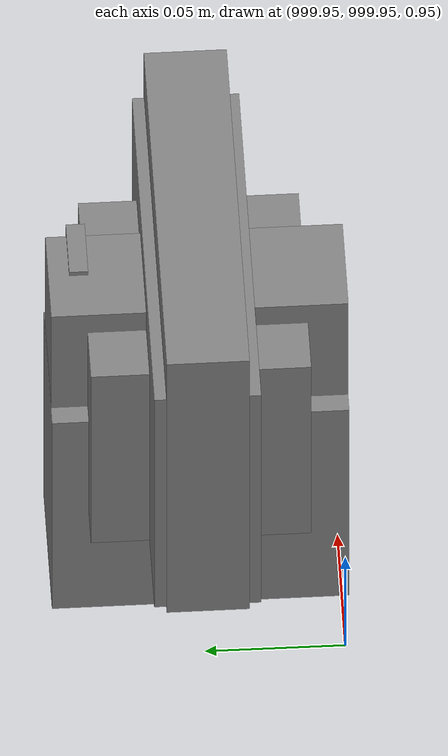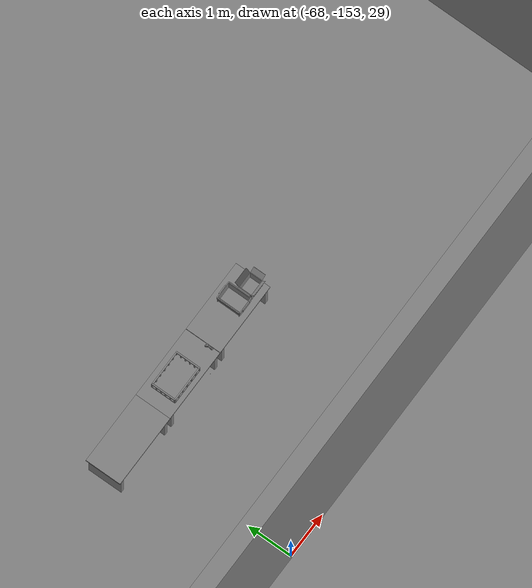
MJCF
<mujoco>
    <option gravity="0.000000000 0.000000000 -9.810000420" timestep="0.0049999999" integrator="implicitfast" density="1.225" viscosity="1.8000001e-05" noslip_iterations="10" iterations="100" sdf_iterations="50">
        <flag multiccd="disable"/>
    </option>
    <size memory="1000M"/>
    <compiler coordinate="local"/>
    <worldbody>
        <light cutoff="30" pos="0 1 1" dir="0 -1 -2"/>
        <light cutoff="30" pos="0 -1 1" dir="0 1 -2"/>
        <body pos="1000.000000000 1000.000000000 1.000000000" euler="0.000011953 0.000005123 -179.999984741" name="openloong_gripper_2f85_fix_base_usda_intel_box">
            <geom contype="1" conaffinity="1" density="1000" type="box" material="" rgba="0.500000000 0.500000000 0.500000000 1.000000000" solimp="0.899999976 0.949999988 0.001000000" friction="1.000000000 0.005000000 0.000100000" solref="0.020000000 1.000000000" margin="0" condim="3" group="0" pos="0.000000000 -0.000067139 0.000082284" quat="0.707106709 0.000000225 0.000000253 0.707106650" size="0.052800003 0.025300000 0.052800003" name="openloong_gripper_2f85_fix_base_usda_geom_E91EF2A6_A7BA_407C_B1BB_0EC97FFC92A1"/>
            <freejoint name="openloong_gripper_2f85_fix_base_usda_intel_box_joint"/>
            <site size="0.005000000 0.005000000 0.005000000" rgba="0.500000000 0.500000000 0.500000000 1.000000000" pos="0.000000000 0.000000000 0.000000000" quat="0.999961913 0.008726500 0.000000000 0.000000000" group="0" type="sphere" name="openloong_gripper_2f85_fix_base_usda_intel_boxsite"/>
        </body>
        <body pos="1000.000000000 1000.000000000 1.000000000" euler="0.000000000 0.000000000 180.000000000" name="openloong_gripper_2f85_fix_base_usda_cpu_fan">
            <geom contype="1" conaffinity="1" density="1000" type="box" material="" rgba="0.500000000 0.500000000 0.500000000 1.000000000" solimp="0.899999976 0.949999988 0.001000000" friction="1.000000000 0.005000000 0.000100000" solref="0.020000000 1.000000000" margin="0" condim="3" group="0" pos="0.000000000 0.000000000 0.070034981" quat="0.000000000 0.000000000 0.000000000 1.000000000" size="0.070700005 0.014699999 0.070700005" name="openloong_gripper_2f85_fix_base_usda_geom_2B74C495_2D5E_4E01_A612_D3F440BB7C2A"/>
            <freejoint name="openloong_gripper_2f85_fix_base_usda_cpu_fan_joint"/>
            <site size="0.005000000 0.005000000 0.005000000" rgba="0.500000000 0.500000000 0.500000000 1.000000000" pos="0.000000000 0.000000000 0.000000000" quat="0.999961913 0.008726535 0.000000000 0.000000000" group="0" type="sphere" name="openloong_gripper_2f85_fix_base_usda_cpu_fancsite"/>
        </body>
        <body pos="1000.000000000 1000.000000000 1.000000000" euler="0.000000000 0.000000000 180.000000000" name="openloong_gripper_2f85_fix_base_usda_wifi_box">
            <geom contype="1" conaffinity="1" density="1000" type="box" material="" rgba="0.500000000 0.500000000 0.500000000 1.000000000" solimp="0.899999976 0.949999988 0.001000000" friction="1.000000000 0.005000000 0.000100000" solref="0.020000000 1.000000000" margin="0" condim="3" group="0" pos="0.000000000 0.000000000 0.058978677" quat="0.000000000 0.000000047 0.000000000 1.000000000" size="0.068499997 0.018999999 0.059000000" name="openloong_gripper_2f85_fix_base_usda_geom_FEC910BA_AC9A_4A62_9713_476CB227F05E"/>
            <freejoint name="openloong_gripper_2f85_fix_base_usda_wifi_box_joint"/>
            <site size="0.005000000 0.005000000 0.005000000" rgba="0.500000000 0.500000000 0.500000000 1.000000000" pos="0.000000000 0.000000000 0.000000000" quat="0.999961913 0.008726500 0.000000000 0.000000000" group="0" type="sphere" name="openloong_gripper_2f85_fix_base_usda_wifi_boxsite"/>
        </body>
        <body pos="-65.946823120 -148.895736694 31.165637970" euler="122.703956604 74.769226074 -89.845573425" mocap="true" name="spotlight6_SpotLight"/>
        <body pos="-66.101882935 -149.448822021 31.163633347" euler="5.533040524 66.261222839 102.462791443" mocap="true" name="spotlight3_SpotLight"/>
        <body pos="1000.000000000 999.999938965 1.000000000" euler="0.000000000 0.000000000 180.000000000" name="openloong_gripper_2f85_fix_base_usda_intelcore_i5">
            <geom contype="1" conaffinity="1" density="1000" type="box" material="" rgba="0.500000000 0.500000000 0.500000000 1.000000000" solimp="0.899999976 0.949999988 0.001000000" friction="1.000000000 0.005000000 0.000100000" solref="0.020000000 1.000000000" margin="0" condim="3" group="0" pos="0.000000000 0.000000000 0.051722717" quat="0.707106709 0.000000000 0.000000000 -0.707106769" size="0.052800000 0.018080002 0.052800000" name="openloong_gripper_2f85_fix_base_usda_geom_659D285E_C3AE_45B3_9085_78B8FC206539"/>
            <freejoint name="openloong_gripper_2f85_fix_base_usda_intelcore_i5_joint"/>
            <site size="0.005000000 0.005000000 0.005000000" rgba="0.500000000 0.500000000 0.500000000 1.000000000" pos="0.000000000 0.000000000 0.000000000" quat="0.999961913 0.008726534 0.000000000 0.000000000" group="0" type="sphere" name="openloong_gripper_2f85_fix_base_usda_intelcore_i5site"/>
        </body>
        <body pos="1000.000000000 1000.000000000 1.000000000" euler="0.000000000 0.000000000 180.000000000" name="openloong_gripper_2f85_fix_base_usda_battery_01">
            <geom contype="1" conaffinity="1" density="1000" type="box" material="" rgba="0.500000000 0.500000000 0.500000000 1.000000000" solimp="0.899999976 0.949999988 0.001000000" friction="1.000000000 0.005000000 0.000100000" solref="0.020000000 1.000000000" margin="0" condim="3" group="0" pos="-0.011123657 -0.041940309 0.101691343" quat="1.000000000 0.000000000 0.000000000 0.000000000" size="0.010800000 0.003375000 0.004725000" name="openloong_gripper_2f85_fix_base_usda_geom_8AB08D98_E101_4DDA_A5C4_605890506FDB"/>
            <geom contype="1" conaffinity="1" density="1000" type="box" material="" rgba="0.500000000 0.500000000 0.500000000 1.000000000" solimp="0.899999976 0.949999988 0.001000000" friction="1.000000000 0.005000000 0.000100000" solref="0.020000000 1.000000000" margin="0" condim="3" group="0" pos="-0.010876465 -0.044247437 0.047066893" quat="0.998702705 -0.050920475 0.000000000 0.000000000" size="0.009450001 0.002700000 0.024975000" name="openloong_gripper_2f85_fix_base_usda_geom_21FBA8C3_A445_4E2D_AB0B_C60CF4A5866D"/>
            <geom contype="1" conaffinity="1" density="1000" type="box" material="" rgba="0.500000000 0.500000000 0.500000000 1.000000000" solimp="0.899999976 0.949999988 0.001000000" friction="1.000000000 0.005000000 0.000100000" solref="0.020000000 1.000000000" margin="0" condim="3" group="0" pos="-0.001235962 -0.000659180 0.047381196" quat="1.000000000 0.000000000 0.000000000 0.000000000" size="0.039420001 0.039150000 0.047250003" name="openloong_gripper_2f85_fix_base_usda_geom_4C3D2B95_FEC5_4814_B7E4_524D84E70FDF"/>
            <geom contype="1" conaffinity="1" density="1000" type="box" material="" rgba="0.500000000 0.500000000 0.500000000 1.000000000" solimp="0.899999976 0.949999988 0.001000000" friction="1.000000000 0.005000000 0.000100000" solref="0.020000000 1.000000000" margin="0" condim="3" group="0" pos="-0.010876465 -0.039138794 0.009851727" quat="1.000000000 0.000000000 0.000000000 0.000000000" size="0.009450001 0.010800000 0.013500000" name="openloong_gripper_2f85_fix_base_usda_geom_00280BA6_704D_4DAB_AAE6_400C0478D2F4"/>
            <geom contype="1" conaffinity="1" density="1000" type="box" material="" rgba="0.500000000 0.500000000 0.500000000 1.000000000" solimp="0.899999976 0.949999988 0.001000000" friction="1.000000000 0.005000000 0.000100000" solref="0.020000000 1.000000000" margin="0" condim="3" group="0" pos="-0.010876465 -0.041528322 0.071508206" quat="1.000000000 0.000000000 0.000000000 0.000000000" size="0.009450001 0.002700000 0.027000001" name="openloong_gripper_2f85_fix_base_usda_geom_9E118CE1_7865_4F48_B0AF_CAEF53F292C1"/>
            <freejoint name="openloong_gripper_2f85_fix_base_usda_battery_01_joint"/>
            <site size="0.005000000 0.005000000 0.005000000" rgba="0.500000000 0.500000000 0.500000000 1.000000000" pos="0.000000000 0.000000000 0.000000000" quat="0.999961913 0.008726500 0.000000000 0.000000000" group="0" type="sphere" name="openloong_gripper_2f85_fix_base_usda_battery_01site"/>
        </body>
        <body pos="-65.929473877 -149.488647461 31.166706085" euler="160.124038696 48.898029327 113.648452759" mocap="true" name="spotlight4_SpotLight"/>
        <body pos="-64.866622925 -149.383972168 30.183746338" euler="89.999984741 89.999946594 0.000000000" name="openloong_gripper_2f85_fix_base_usda_bluebox_01">
            <geom contype="1" conaffinity="1" density="1000" type="box" material="" rgba="0.500000000 0.500000000 0.500000000 1.000000000" solimp="0.899999976 0.949999988 0.001000000" friction="1.000000000 0.005000000 0.000100000" solref="0.020000000 1.000000000" margin="0" condim="3" group="0" pos="0.276580811 0.187225342 0.000068665" quat="0.707106948 0.000077471 0.707106352 0.000077486" size="0.100000001 0.057999998 0.010000000" name="openloong_gripper_2f85_fix_base_usda_geom_5401DF45_C535_46E4_8118_0DC4E9953589"/>
            <geom contype="1" conaffinity="1" density="1000" type="box" material="" rgba="0.500000000 0.500000000 0.500000000 1.000000000" solimp="0.899999976 0.949999988 0.001000000" friction="1.000000000 0.005000000 0.000100000" solref="0.020000000 1.000000000" margin="0" condim="3" group="0" pos="0.000000000 0.002883911 0.000000000" quat="0.999999881 0.000000000 0.000000000 0.000000000" size="0.254000008 0.003000000 0.172000006" name="openloong_gripper_2f85_fix_base_usda_geom_2ACEF641_F76C_43C3_BA4B_A3083651ABE4"/>
            <geom contype="1" conaffinity="1" density="1000" type="box" material="" rgba="0.500000000 0.500000000 0.500000000 1.000000000" solimp="0.899999976 0.949999988 0.001000000" friction="1.000000000 0.005000000 0.000100000" solref="0.020000000 1.000000000" margin="0" condim="3" group="0" pos="0.000000000 0.124874115 0.173484802" quat="0.999796331 0.020176515 -0.000000015 0.000000030" size="0.259999990 0.119999997 0.007000000" name="openloong_gripper_2f85_fix_base_usda_geom_055A2E38_CBF8_4A01_92F9_F887B3B63EDC"/>
            <geom contype="1" conaffinity="1" density="1000" type="box" material="" rgba="0.500000000 0.500000000 0.500000000 1.000000000" solimp="0.899999976 0.949999988 0.001000000" friction="1.000000000 0.005000000 0.000100000" solref="0.020000000 1.000000000" margin="0" condim="3" group="0" pos="0.000000000 0.124874115 -0.173469543" quat="0.999796331 -0.020176545 -0.000000015 0.000000000" size="0.259999990 0.119999997 0.007000000" name="openloong_gripper_2f85_fix_base_usda_geom_0C458C9F_EC5F_423C_A562_52782BF7964E"/>
            <geom contype="1" conaffinity="1" density="1000" type="box" material="" rgba="0.500000000 0.500000000 0.500000000 1.000000000" solimp="0.899999976 0.949999988 0.001000000" friction="1.000000000 0.005000000 0.000100000" solref="0.020000000 1.000000000" margin="0" condim="3" group="0" pos="0.000000000 0.214008331 0.188980103" quat="0.999912977 0.013176724 0.000000015 0.000000000" size="0.259999990 0.029999999 0.012500000" name="openloong_gripper_2f85_fix_base_usda_geom_47596DB4_0610_442E_B8D7_B6684D452F13"/>
            <geom contype="1" conaffinity="1" density="1000" type="box" material="" rgba="0.500000000 0.500000000 0.500000000 1.000000000" solimp="0.899999976 0.949999988 0.001000000" friction="1.000000000 0.005000000 0.000100000" solref="0.020000000 1.000000000" margin="0" condim="3" group="0" pos="-0.258361816 0.125289917 0.001876831" quat="0.702796936 -0.020792112 0.710783124 0.020769298" size="0.189999998 0.119999997 0.009000000" name="openloong_gripper_2f85_fix_base_usda_geom_E8F3F8B3_22A1_4D36_BF3F_851086A4C141"/>
            <geom contype="1" conaffinity="1" density="1000" type="box" material="" rgba="0.500000000 0.500000000 0.500000000 1.000000000" solimp="0.899999976 0.949999988 0.001000000" friction="1.000000000 0.005000000 0.000100000" solref="0.020000000 1.000000000" margin="0" condim="3" group="0" pos="0.000000000 0.214008331 -0.188980103" quat="0.999912977 -0.013176769 0.000000030 0.000000015" size="0.259999990 0.029999999 0.012500000" name="openloong_gripper_2f85_fix_base_usda_geom_62A7A5BA_AB43_4A74_B422_06C713AAD075"/>
            <geom contype="1" conaffinity="1" density="1000" type="box" material="" rgba="0.500000000 0.500000000 0.500000000 1.000000000" solimp="0.899999976 0.949999988 0.001000000" friction="1.000000000 0.005000000 0.000100000" solref="0.020000000 1.000000000" margin="0" condim="3" group="0" pos="-0.276611328 0.187225342 0.000068665" quat="0.707106650 0.000077441 0.707106709 0.000077456" size="0.100000001 0.057999998 0.010000000" name="openloong_gripper_2f85_fix_base_usda_geom_4D2701B5_87F2_4D4A_8008_414B59F46707"/>
            <geom contype="1" conaffinity="1" density="1000" type="box" material="" rgba="0.500000000 0.500000000 0.500000000 1.000000000" solimp="0.899999976 0.949999988 0.001000000" friction="1.000000000 0.005000000 0.000100000" solref="0.020000000 1.000000000" margin="0" condim="3" group="0" pos="0.258331299 0.125289917 0.001876831" quat="0.702851415 0.018856421 0.710823774 -0.019329369" size="0.189999998 0.119999997 0.009000000" name="openloong_gripper_2f85_fix_base_usda_geom_5070A89B_4F1D_48A8_8CB0_D0EA348F66A3"/>
            <freejoint name="openloong_gripper_2f85_fix_base_usda_bluebox_01_joint"/>
            <site size="0.005000000 0.005000000 0.005000000" rgba="0.500000000 0.500000000 0.500000000 1.000000000" pos="0.000000000 0.000000000 0.000000000" quat="0.999961913 0.008726534 0.000000000 0.000000000" group="0" type="sphere" name="openloong_gripper_2f85_fix_base_usda_bluebox_01site"/>
        </body>
        <body pos="-64.496299744 -149.491867065 30.235729218" euler="0.000000000 0.000000000 89.999946594" name="openloong_gripper_2f85_fix_base_usda_cardboardbox_01">
            <geom contype="1" conaffinity="1" density="1000" type="box" material="" rgba="0.500000000 0.500000000 0.500000000 1.000000000" solimp="0.899999976 0.949999988 0.001000000" friction="1.000000000 0.005000000 0.000100000" solref="0.020000000 1.000000000" margin="0" condim="3" group="0" pos="-0.003166199 -0.004086494 0.005052090" quat="1.000000000 0.000000000 0.000000000 0.000000000" size="0.142499998 0.177500010 0.005000000" name="openloong_gripper_2f85_fix_base_usda_geom_995B15F4_7AC6_4A40_98A7_B31DB47688B1"/>
            <geom contype="1" conaffinity="1" density="1000" type="box" material="" rgba="0.500000000 0.500000000 0.500000000 1.000000000" solimp="0.899999976 0.949999988 0.001000000" friction="1.000000000 0.005000000 0.000100000" solref="0.020000000 1.000000000" margin="0" condim="3" group="0" pos="-0.003166199 0.170316696 0.150570869" quat="1.000000000 0.000000000 0.000000000 0.000000000" size="0.142499998 0.005000000 0.149999991" name="openloong_gripper_2f85_fix_base_usda_geom_52199F93_A6D1_4BF0_808E_8DD76D10C0C0"/>
            <geom contype="1" conaffinity="1" density="1000" type="box" material="" rgba="0.500000000 0.500000000 0.500000000 1.000000000" solimp="0.899999976 0.949999988 0.001000000" friction="1.000000000 0.005000000 0.000100000" solref="0.020000000 1.000000000" margin="0" condim="3" group="0" pos="-0.147399902 -0.005307198 0.150570869" quat="1.000000000 0.000000000 0.000000000 0.000000000" size="0.005000000 0.177500010 0.149999991" name="openloong_gripper_2f85_fix_base_usda_geom_11EB59B5_54CD_4028_82D7_DE54931347A7"/>
            <geom contype="1" conaffinity="1" density="1000" type="box" material="" rgba="0.500000000 0.500000000 0.500000000 1.000000000" solimp="0.899999976 0.949999988 0.001000000" friction="1.000000000 0.005000000 0.000100000" solref="0.020000000 1.000000000" margin="0" condim="3" group="0" pos="0.140275955 -0.005307198 0.150570869" quat="1.000000000 0.000000000 0.000000000 0.000000000" size="0.005000000 0.177500010 0.149999991" name="openloong_gripper_2f85_fix_base_usda_geom_D6BE21F8_7B3A_4C5F_88C8_6A1E9F875A77"/>
            <geom contype="1" conaffinity="1" density="1000" type="box" material="" rgba="0.500000000 0.500000000 0.500000000 1.000000000" solimp="0.899999976 0.949999988 0.001000000" friction="1.000000000 0.005000000 0.000100000" solref="0.020000000 1.000000000" margin="0" condim="3" group="0" pos="-0.003166199 -0.181550980 0.150570869" quat="1.000000000 0.000000000 0.000000000 0.000000000" size="0.142499998 0.005000000 0.149999991" name="openloong_gripper_2f85_fix_base_usda_geom_A24AF4DB_10CB_4F72_80A0_DEDCD60CCCA5"/>
            <freejoint name="openloong_gripper_2f85_fix_base_usda_cardboardbox_01_joint"/>
            <site size="0.005000000 0.005000000 0.005000000" rgba="0.500000000 0.500000000 0.500000000 1.000000000" pos="0.000000000 0.000000000 0.000000000" quat="0.999961913 0.008726535 0.000000000 0.000000000" group="0" type="sphere" name="openloong_gripper_2f85_fix_base_usda_site_6BBBF97B_7C67_4CF5_9CC8_0CF9FED665E4"/>
            <body pos="0.139160156 -0.004048347 0.301930904" euler="-179.999954224 49.383502960 179.999954224" name="openloong_gripper_2f85_fix_base_usda_A1_006">
                <geom contype="1" conaffinity="1" density="1000" type="box" material="" rgba="0.500000000 0.500000000 0.500000000 1.000000000" solimp="0.899999976 0.949999988 0.001000000" friction="1.000000000 0.005000000 0.000100000" solref="0.020000000 1.000000000" margin="0" condim="3" group="0" pos="-0.071587563 0.000009537 0.001745224" quat="0.999999881 0.000000000 0.000000000 0.000000000" size="0.071249999 0.179999992 0.002500000" name="openloong_gripper_2f85_fix_base_usda_geom_6B5AF741_18D8_4B81_95FE_BAA8377757DA"/>
                <joint armature="0" stiffness="0.07" damping="0.0099999998" axis="0.000000 1.000000 0.000000" type="hinge" name="openloong_gripper_2f85_fix_base_usda_A1_006"/>
            </body>
            <body pos="-0.145902634 -0.004086494 0.301938057" euler="-180.000000000 -60.000011444 -180.000000000" name="openloong_gripper_2f85_fix_base_usda_A2_006">
                <geom contype="1" conaffinity="1" density="1000" type="box" material="" rgba="0.500000000 0.500000000 0.500000000 1.000000000" solimp="0.899999976 0.949999988 0.001000000" friction="1.000000000 0.005000000 0.000100000" solref="0.020000000 1.000000000" margin="0" condim="3" group="0" pos="0.071268082 0.000009537 0.002717972" quat="0.000002921 0.000000000 -0.000000030 0.999999881" size="0.071249999 0.179999992 0.002500000" name="openloong_gripper_2f85_fix_base_usda_geom_292F5944_4671_4E79_8B31_9DAE7529E440"/>
                <joint armature="0" stiffness="0.07" damping="0.0099999998" axis="0.000000 1.000000 0.000000" type="hinge" name="openloong_gripper_2f85_fix_base_usda_A2_006"/>
            </body>
            <body pos="-0.003385544 0.175991058 0.301930904" euler="-125.858116150 -0.000004561 0.000002331" name="openloong_gripper_2f85_fix_base_usda_B2_006">
                <geom contype="1" conaffinity="1" density="1000" type="box" material="" rgba="0.500000000 0.500000000 0.500000000 1.000000000" solimp="0.899999976 0.949999988 0.001000000" friction="1.000000000 0.005000000 0.000100000" solref="0.020000000 1.000000000" margin="0" condim="3" group="0" pos="0.000009537 -0.070939064 -0.002470016" quat="0.999614120 0.027776197 -0.000000015 0.000000030" size="0.137500003 0.064999998 0.005000000" name="openloong_gripper_2f85_fix_base_usda_geom_8E229981_33B7_45E2_AED4_428E5708817B"/>
                <joint armature="0" stiffness="0.07" damping="0.0099999998" axis="1.000000 0.000000 0.000000" type="hinge" name="openloong_gripper_2f85_fix_base_usda_B2_006"/>
            </body>
            <body pos="-0.003385544 -0.184140205 0.301938057" euler="147.805557251 0.000000000 0.000000000" name="openloong_gripper_2f85_fix_base_usda_B1_006">
                <geom contype="1" conaffinity="1" density="1000" type="box" material="" rgba="0.500000000 0.500000000 0.500000000 1.000000000" solimp="0.899999976 0.949999988 0.001000000" friction="1.000000000 0.005000000 0.000100000" solref="0.020000000 1.000000000" margin="0" condim="3" group="0" pos="-0.000028610 0.070202351 -0.002703667" quat="0.999614179 -0.027776167 0.000000000 0.000000000" size="0.137500003 0.064999998 0.005000000" name="openloong_gripper_2f85_fix_base_usda_geom_AC44EB27_1F44_4417_9A7A_7ABC466BA4E4"/>
                <joint armature="0" stiffness="0.07" damping="0.0099999998" axis="1.000000 0.000000 0.000000" type="hinge" name="openloong_gripper_2f85_fix_base_usda_B1_006"/>
            </body>
        </body>
        <body pos="-65.882858276 -149.481979370 30.229999542" euler="-64.487716675 0.000000000 0.000000000" name="openloong_gripper_2f85_fix_base_usda_Barcode">
            <geom contype="1" conaffinity="1" density="1000" type="box" material="" rgba="0.500000000 0.500000000 0.500000000 1.000000000" solimp="0.899999976 0.949999988 0.001000000" friction="1.000000000 0.005000000 0.000100000" solref="0.020000000 1.000000000" margin="0" condim="3" group="0" pos="0.000000000 0.013038635 0.001419067" quat="0.000000000 0.000000000 0.000000000 1.000000119" size="0.034000002 0.010000000 0.017999999" name="openloong_gripper_2f85_fix_base_usda_geom_FDE1B387_8C1A_4425_97DE_0B78638BE0C6"/>
            <geom contype="1" conaffinity="1" density="1000" type="box" material="" rgba="0.500000000 0.500000000 0.500000000 1.000000000" solimp="0.899999976 0.949999988 0.001000000" friction="1.000000000 0.005000000 0.000100000" solref="0.020000000 1.000000000" margin="0" condim="3" group="0" pos="0.000000000 -0.035301208 -0.007095337" quat="0.000000000 0.000000000 -0.043619365 0.999048233" size="0.028999999 0.010000000 0.020000000" name="openloong_gripper_2f85_fix_base_usda_geom_EB641881_52F9_4C64_8549_8DDA48A5AE81"/>
            <geom contype="1" conaffinity="1" density="1000" type="box" material="" rgba="0.500000000 0.500000000 0.500000000 1.000000000" solimp="0.899999976 0.949999988 0.001000000" friction="1.000000000 0.005000000 0.000100000" solref="0.020000000 1.000000000" margin="0" condim="3" group="0" pos="0.000000000 -0.043411255 -0.011749268" quat="0.922262907 0.386563420 0.000000000 0.000000000" size="0.026000001 0.010000000 0.020000000" name="openloong_gripper_2f85_fix_base_usda_geom_C361BC25_35EE_4CFA_BD4B_3F079BE193BB"/>
            <geom contype="1" conaffinity="1" density="1000" type="box" material="" rgba="0.500000000 0.500000000 0.500000000 1.000000000" solimp="0.899999976 0.949999988 0.001000000" friction="1.000000000 0.005000000 0.000100000" solref="0.020000000 1.000000000" margin="0" condim="3" group="0" pos="0.000000000 -0.016967773 -0.031860352" quat="0.000000000 0.000000000 0.000000000 1.000000119" size="0.008000000 0.010000000 0.013000000" name="openloong_gripper_2f85_fix_base_usda_geom_8230FE68_988A_4F1D_9BD8_263FB7053C1E"/>
            <geom contype="1" conaffinity="1" density="1000" type="box" material="" rgba="0.500000000 0.500000000 0.500000000 1.000000000" solimp="0.899999976 0.949999988 0.001000000" friction="1.000000000 0.005000000 0.000100000" solref="0.020000000 1.000000000" margin="0" condim="3" group="0" pos="0.000000000 -0.001869202 0.000312805" quat="0.953716993 0.300705761 0.000000000 0.000000000" size="0.032000002 0.010000000 0.018999999" name="openloong_gripper_2f85_fix_base_usda_geom_8F7BEB6A_94AC_49E0_A554_5999B5559C81"/>
            <geom contype="1" conaffinity="1" density="1000" type="box" material="" rgba="0.500000000 0.500000000 0.500000000 1.000000000" solimp="0.899999976 0.949999988 0.001000000" friction="1.000000000 0.005000000 0.000100000" solref="0.020000000 1.000000000" margin="0" condim="3" group="0" pos="0.000000000 -0.019531250 -0.003173828" quat="0.953716993 0.300705761 0.000000000 0.000000000" size="0.030999999 0.010000000 0.020000000" name="openloong_gripper_2f85_fix_base_usda_geom_7597CDD4_DEE7_45E7_AB15_F820A18528F6"/>
            <geom contype="1" conaffinity="1" density="1000" type="box" material="" rgba="0.500000000 0.500000000 0.500000000 1.000000000" solimp="0.899999976 0.949999988 0.001000000" friction="1.000000000 0.005000000 0.000100000" solref="0.020000000 1.000000000" margin="0" condim="3" group="0" pos="0.000000000 -0.035301208 -0.007095337" quat="0.953716993 0.300705761 0.000000000 0.000000000" size="0.028999999 0.010000000 0.020000000" name="openloong_gripper_2f85_fix_base_usda_geom_904CDB35_A129_49F4_920F_FCDA2C671D57"/>
            <geom contype="1" conaffinity="1" density="1000" type="box" material="" rgba="0.500000000 0.500000000 0.500000000 1.000000000" solimp="0.899999976 0.949999988 0.001000000" friction="1.000000000 0.005000000 0.000100000" solref="0.020000000 1.000000000" margin="0" condim="3" group="0" pos="0.000000000 -0.042617798 -0.071121216" quat="0.000000000 0.000000000 0.000000000 1.000000119" size="0.013000000 0.021000000 0.059999999" name="openloong_gripper_2f85_fix_base_usda_geom_F51ED14C_1E44_4CF6_9FFF_04B721DCEED1"/>
            <freejoint name="openloong_gripper_2f85_fix_base_usda_Barcode_joint"/>
            <site size="0.005000000 0.005000000 0.005000000" rgba="0.500000000 0.500000000 0.500000000 1.000000000" pos="0.000000000 0.000000000 0.000000000" quat="1.000000000 0.000000000 0.000000000 0.000000000" group="0" type="sphere" name="openloong_gripper_2f85_fix_base_usda_Barcode_site"/>
        </body>
        <body pos="-66.745018005 -149.392349243 30.184000015" euler="0.000000000 0.000000000 89.999946594" name="[22331291347702]_Basket_01">
            <geom contype="1" conaffinity="1" density="1000" type="box" material="" rgba="0.500000000 0.500000000 0.500000000 1.000000000" solimp="0.899999976 0.949999988 0.001000000" friction="1.000000000 0.005000000 0.000100000" solref="0.020000000 1.000000000" margin="0" condim="3" group="0" pos="-0.052425385 0.389207840 0.089787483" quat="0.707107008 0.000000000 0.000000000 0.707106411" size="0.014249999 0.014249999 0.059999999" name="[22331291347702]_geom_66A740F8_7FD8_4D11_9769_69EEBB404E4D"/>
            <geom contype="1" conaffinity="1" density="1000" type="box" material="" rgba="0.500000000 0.500000000 0.500000000 1.000000000" solimp="0.899999976 0.949999988 0.001000000" friction="1.000000000 0.005000000 0.000100000" solref="0.020000000 1.000000000" margin="0" condim="3" group="0" pos="0.264015198 -0.133043289 0.089787483" quat="0.707107008 0.000000000 0.000000000 0.707106411" size="0.014249999 0.014249999 0.059999999" name="[22331291347702]_geom_B12AF3A0_E297_48CC_845D_7DC5F90E2F92"/>
            <geom contype="1" conaffinity="1" density="1000" type="box" material="" rgba="0.500000000 0.500000000 0.500000000 1.000000000" solimp="0.899999976 0.949999988 0.001000000" friction="1.000000000 0.005000000 0.000100000" solref="0.020000000 1.000000000" margin="0" condim="3" group="0" pos="-0.264015198 -0.265548706 0.089793205" quat="0.707107008 0.000000000 0.000000000 0.707106411" size="0.014249999 0.014249999 0.059999999" name="[22331291347702]_geom_0420CD94_C5CF_4E15_833B_D84F93716D6E"/>
            <geom contype="1" conaffinity="1" density="1000" type="box" material="" rgba="0.500000000 0.500000000 0.500000000 1.000000000" solimp="0.899999976 0.949999988 0.001000000" friction="1.000000000 0.005000000 0.000100000" solref="0.020000000 1.000000000" margin="0" condim="3" group="0" pos="-0.160263062 -0.389322281 0.089793205" quat="0.707107008 0.000000000 0.000000000 0.707106411" size="0.014249999 0.014249999 0.059999999" name="[22331291347702]_geom_5219D521_03D2_454C_83EF_A6963B503D1C"/>
            <geom contype="1" conaffinity="1" density="1000" type="box" material="" rgba="0.500000000 0.500000000 0.500000000 1.000000000" solimp="0.899999976 0.949999988 0.001000000" friction="1.000000000 0.005000000 0.000100000" solref="0.020000000 1.000000000" margin="0" condim="3" group="0" pos="0.162265778 -0.389322281 0.089787483" quat="0.707107008 0.000000000 0.000000000 0.707106411" size="0.014249999 0.014249999 0.059999999" name="[22331291347702]_geom_3BFE9579_E01D_4943_9110_4FDFFC3EF2DC"/>
            <geom contype="1" conaffinity="1" density="1000" type="box" material="" rgba="0.500000000 0.500000000 0.500000000 1.000000000" solimp="0.899999976 0.949999988 0.001000000" friction="1.000000000 0.005000000 0.000100000" solref="0.020000000 1.000000000" margin="0" condim="3" group="0" pos="0.264015198 0.389207840 0.089787483" quat="0.707107008 0.000000000 0.000000000 0.707106411" size="0.014249999 0.014249999 0.059999999" name="[22331291347702]_geom_7F62A7D6_1A46_4B06_92D3_8A755E8AB670"/>
            <geom contype="1" conaffinity="1" density="1000" type="box" material="" rgba="0.500000000 0.500000000 0.500000000 1.000000000" solimp="0.899999976 0.949999988 0.001000000" friction="1.000000000 0.005000000 0.000100000" solref="0.020000000 1.000000000" margin="0" condim="3" group="0" pos="-0.264015198 -0.133043289 0.089793205" quat="0.707107008 0.000000000 0.000000000 0.707106411" size="0.014249999 0.014249999 0.059999999" name="[22331291347702]_geom_DA577559_1CBE_4682_89CF_E3B202AF669E"/>
            <geom contype="1" conaffinity="1" density="1000" type="box" material="" rgba="0.500000000 0.500000000 0.500000000 1.000000000" solimp="0.899999976 0.949999988 0.001000000" friction="1.000000000 0.005000000 0.000100000" solref="0.020000000 1.000000000" margin="0" condim="3" group="0" pos="-0.264026642 0.269256592 0.089793205" quat="0.707107008 0.000000000 0.000000000 0.707106411" size="0.014249999 0.014249999 0.059999999" name="[22331291347702]_geom_AB7DAFDC_83CB_4AC2_861A_C5FF0620C1A9"/>
            <geom contype="1" conaffinity="1" density="1000" type="box" material="" rgba="0.500000000 0.500000000 0.500000000 1.000000000" solimp="0.899999976 0.949999988 0.001000000" friction="1.000000000 0.005000000 0.000100000" solref="0.020000000 1.000000000" margin="0" condim="3" group="0" pos="0.054462433 0.389207840 0.089787483" quat="0.707107008 0.000000000 0.000000000 0.707106411" size="0.014249999 0.014249999 0.059999999" name="[22331291347702]_geom_3EBBB92C_EAE8_468D_806B_3863A177823C"/>
            <geom contype="1" conaffinity="1" density="1000" type="box" material="" rgba="0.500000000 0.500000000 0.500000000 1.000000000" solimp="0.899999976 0.949999988 0.001000000" friction="1.000000000 0.005000000 0.000100000" solref="0.020000000 1.000000000" margin="0" condim="3" group="0" pos="0.054462433 -0.389322281 0.089787483" quat="0.707107008 0.000000000 0.000000000 0.707106411" size="0.014249999 0.014249999 0.059999999" name="[22331291347702]_geom_211CBAD3_0D44_472D_BAFD_98FB177212B9"/>
            <geom contype="1" conaffinity="1" density="1000" type="box" material="" rgba="0.500000000 0.500000000 0.500000000 1.000000000" solimp="0.899999976 0.949999988 0.001000000" friction="1.000000000 0.005000000 0.000100000" solref="0.020000000 1.000000000" margin="0" condim="3" group="0" pos="0.264015198 0.269256592 0.089793205" quat="0.707107008 0.000000000 0.000000000 0.707106411" size="0.014249999 0.014249999 0.059999999" name="[22331291347702]_geom_52D59D56_2A70_4894_ACBF_CB5B71C510D7"/>
            <geom contype="1" conaffinity="1" density="1000" type="box" material="" rgba="0.500000000 0.500000000 0.500000000 1.000000000" solimp="0.899999976 0.949999988 0.001000000" friction="1.000000000 0.005000000 0.000100000" solref="0.020000000 1.000000000" margin="0" condim="3" group="0" pos="0.264015198 -0.389322281 0.089787483" quat="0.707107008 0.000000000 0.000000000 0.707106411" size="0.014249999 0.014249999 0.059999999" name="[22331291347702]_geom_E6DA4214_F99E_435E_AB5B_18BA80D36B38"/>
            <geom contype="1" conaffinity="1" density="1000" type="box" material="" rgba="0.500000000 0.500000000 0.500000000 1.000000000" solimp="0.899999976 0.949999988 0.001000000" friction="1.000000000 0.005000000 0.000100000" solref="0.020000000 1.000000000" margin="0" condim="3" group="0" pos="0.000000000 0.000000000 0.015998840" quat="0.707107008 0.000000000 0.000000000 0.707106411" size="0.403499991 0.279000014 0.015750000" name="[22331291347702]_geom_84276923_7650_4D12_BEC3_67B2282E39EA"/>
            <geom contype="1" conaffinity="1" density="1000" type="box" material="" rgba="0.500000000 0.500000000 0.500000000 1.000000000" solimp="0.899999976 0.949999988 0.001000000" friction="1.000000000 0.005000000 0.000100000" solref="0.020000000 1.000000000" margin="0" condim="3" group="0" pos="0.000000000 -0.389476776 0.163619041" quat="0.707107008 0.000000000 0.000000000 0.707106411" size="0.015000000 0.277500004 0.015750000" name="[22331291347702]_geom_CE23379F_181F_483E_AFAA_BBEBA77DC438"/>
            <geom contype="1" conaffinity="1" density="1000" type="box" material="" rgba="0.500000000 0.500000000 0.500000000 1.000000000" solimp="0.899999976 0.949999988 0.001000000" friction="1.000000000 0.005000000 0.000100000" solref="0.020000000 1.000000000" margin="0" condim="3" group="0" pos="0.162265778 0.389207840 0.089787483" quat="0.707107008 0.000000000 0.000000000 0.707106411" size="0.014249999 0.014249999 0.059999999" name="[22331291347702]_geom_F8CE261A_B7E6_42C9_A477_E8028CC643AD"/>
            <geom contype="1" conaffinity="1" density="1000" type="box" material="" rgba="0.500000000 0.500000000 0.500000000 1.000000000" solimp="0.899999976 0.949999988 0.001000000" friction="1.000000000 0.005000000 0.000100000" solref="0.020000000 1.000000000" margin="0" condim="3" group="0" pos="0.000000000 0.389471054 0.163619041" quat="0.707107008 0.000000000 0.000000000 0.707106411" size="0.015000000 0.277500004 0.015750000" name="[22331291347702]_geom_3DDDE091_E845_4968_BBF1_659B4F392048"/>
            <geom contype="1" conaffinity="1" density="1000" type="box" material="" rgba="0.500000000 0.500000000 0.500000000 1.000000000" solimp="0.899999976 0.949999988 0.001000000" friction="1.000000000 0.005000000 0.000100000" solref="0.020000000 1.000000000" margin="0" condim="3" group="0" pos="-0.263511658 0.000000000 0.163619041" quat="0.707107008 0.000000000 0.000000000 0.707106411" size="0.403499991 0.015000000 0.015750000" name="[22331291347702]_geom_430B5718_879E_40C2_9750_7DAD03685288"/>
            <geom contype="1" conaffinity="1" density="1000" type="box" material="" rgba="0.500000000 0.500000000 0.500000000 1.000000000" solimp="0.899999976 0.949999988 0.001000000" friction="1.000000000 0.005000000 0.000100000" solref="0.020000000 1.000000000" margin="0" condim="3" group="0" pos="-0.264015198 0.141334534 0.089793205" quat="0.707107008 0.000000000 0.000000000 0.707106411" size="0.014249999 0.014249999 0.059999999" name="[22331291347702]_geom_F9F2D39A_976C_466F_8AC4_257A299F6E2E"/>
            <geom contype="1" conaffinity="1" density="1000" type="box" material="" rgba="0.500000000 0.500000000 0.500000000 1.000000000" solimp="0.899999976 0.949999988 0.001000000" friction="1.000000000 0.005000000 0.000100000" solref="0.020000000 1.000000000" margin="0" condim="3" group="0" pos="0.264015198 -0.265548706 0.089787483" quat="0.707107008 0.000000000 0.000000000 0.707106411" size="0.014249999 0.014249999 0.059999999" name="[22331291347702]_geom_A7B9D709_6FAA_45CB_ADF1_66D909977799"/>
            <geom contype="1" conaffinity="1" density="1000" type="box" material="" rgba="0.500000000 0.500000000 0.500000000 1.000000000" solimp="0.899999976 0.949999988 0.001000000" friction="1.000000000 0.005000000 0.000100000" solref="0.020000000 1.000000000" margin="0" condim="3" group="0" pos="-0.160263062 0.389207840 0.089787483" quat="0.707107008 0.000000000 0.000000000 0.707106411" size="0.014249999 0.014249999 0.059999999" name="[22331291347702]_geom_DBB58069_15D5_4FC7_BE19_99831A912121"/>
            <geom contype="1" conaffinity="1" density="1000" type="box" material="" rgba="0.500000000 0.500000000 0.500000000 1.000000000" solimp="0.899999976 0.949999988 0.001000000" friction="1.000000000 0.005000000 0.000100000" solref="0.020000000 1.000000000" margin="0" condim="3" group="0" pos="-0.052425385 -0.389322281 0.089787483" quat="0.707107008 0.000000000 0.000000000 0.707106411" size="0.014249999 0.014249999 0.059999999" name="[22331291347702]_geom_63058EC6_645F_4AFD_8F21_6C93E5EB2233"/>
            <geom contype="1" conaffinity="1" density="1000" type="box" material="" rgba="0.500000000 0.500000000 0.500000000 1.000000000" solimp="0.899999976 0.949999988 0.001000000" friction="1.000000000 0.005000000 0.000100000" solref="0.020000000 1.000000000" margin="0" condim="3" group="0" pos="-0.264026642 -0.389322281 0.089793205" quat="0.707107008 0.000000000 0.000000000 0.707106411" size="0.014249999 0.014249999 0.059999999" name="[22331291347702]_geom_076F6FED_B7D8_4AC7_A465_FEA42D37255A"/>
            <geom contype="1" conaffinity="1" density="1000" type="box" material="" rgba="0.500000000 0.500000000 0.500000000 1.000000000" solimp="0.899999976 0.949999988 0.001000000" friction="1.000000000 0.005000000 0.000100000" solref="0.020000000 1.000000000" margin="0" condim="3" group="0" pos="0.264015198 0.141334534 0.089787483" quat="0.707107008 0.000000000 0.000000000 0.707106411" size="0.014249999 0.014249999 0.059999999" name="[22331291347702]_geom_F8413B00_F5B6_43AD_9C7A_4BF75262E830"/>
            <geom contype="1" conaffinity="1" density="1000" type="box" material="" rgba="0.500000000 0.500000000 0.500000000 1.000000000" solimp="0.899999976 0.949999988 0.001000000" friction="1.000000000 0.005000000 0.000100000" solref="0.020000000 1.000000000" margin="0" condim="3" group="0" pos="-0.264015198 0.389207840 0.089793205" quat="0.707107008 0.000000000 0.000000000 0.707106411" size="0.014249999 0.014249999 0.059999999" name="[22331291347702]_geom_1415B6A4_9E59_4CF6_8F3B_45F9F00F769C"/>
            <geom contype="1" conaffinity="1" density="1000" type="box" material="" rgba="0.500000000 0.500000000 0.500000000 1.000000000" solimp="0.899999976 0.949999988 0.001000000" friction="1.000000000 0.005000000 0.000100000" solref="0.020000000 1.000000000" margin="0" condim="3" group="0" pos="0.264015198 0.004480362 0.089787483" quat="0.707107008 0.000000000 0.000000000 0.707106411" size="0.014249999 0.014249999 0.059999999" name="[22331291347702]_geom_F72F9E35_D674_426A_B8D2_2E037018D21B"/>
            <geom contype="1" conaffinity="1" density="1000" type="box" material="" rgba="0.500000000 0.500000000 0.500000000 1.000000000" solimp="0.899999976 0.949999988 0.001000000" friction="1.000000000 0.005000000 0.000100000" solref="0.020000000 1.000000000" margin="0" condim="3" group="0" pos="0.263694763 -0.000011444 0.163619041" quat="0.707107008 0.000000000 0.000000000 0.707106411" size="0.403499991 0.015000000 0.015750000" name="[22331291347702]_geom_ED6D03FB_FC62_4EE1_A8A4_9DEF8A367924"/>
            <geom contype="1" conaffinity="1" density="1000" type="box" material="" rgba="0.500000000 0.500000000 0.500000000 1.000000000" solimp="0.899999976 0.949999988 0.001000000" friction="1.000000000 0.005000000 0.000100000" solref="0.020000000 1.000000000" margin="0" condim="3" group="0" pos="-0.264015198 0.004480362 0.089793205" quat="0.707107008 0.000000000 0.000000000 0.707106411" size="0.014249999 0.014249999 0.059999999" name="[22331291347702]_geom_F240FD46_8968_46CA_BECA_E1F44F4DEBBE"/>
            <freejoint name="[22331291347702]_joint_33061268_258D_43E1_95F2_25C7BEBE7D4F"/>
        </body>
        <body pos="0.000000000 0.000000000 0.000000000" euler="0.000000000 0.000000000 0.000000000" name="Static Objects_Static Objects">
            <geom contype="1" conaffinity="1" density="1000" type="box" material="" rgba="0.500000000 0.500000000 0.500000000 1.000000000" solimp="0.899999976 0.949999988 0.001000000" friction="1.000000000 0.005000000 0.000100000" solref="0.020000000 1.000000000" margin="0" condim="3" group="0" pos="-67.544113159 -149.365814209 29.727830887" quat="0.500000417 0.499999970 0.499999553 0.499999970" size="0.381000012 0.319999993 0.041000001" name="Static Objects_geom_695F0691_0FED_45B0_8841_E7AC6572F6B7"/>
            <geom contype="1" conaffinity="1" density="1000" type="box" material="" rgba="0.500000000 0.500000000 0.500000000 1.000000000" solimp="0.899999976 0.949999988 0.001000000" friction="1.000000000 0.005000000 0.000100000" solref="0.020000000 1.000000000" margin="0" condim="3" group="0" pos="-68.239501953 -149.365814209 30.086868286" quat="0.500000417 0.499999970 0.499999553 0.499999970" size="0.370999992 0.039500002 0.745000005" name="Static Objects_geom_B3EE661E_05A9_4330_AC22_0A9C6857B242"/>
            <geom contype="1" conaffinity="1" density="1000" type="box" material="" rgba="0.500000000 0.500000000 0.500000000 1.000000000" solimp="0.899999976 0.949999988 0.001000000" friction="1.000000000 0.005000000 0.000100000" solref="0.020000000 1.000000000" margin="0" condim="3" group="0" pos="-68.239501953 -149.365814209 30.147235870" quat="0.500000417 0.499999970 0.499999553 0.499999970" size="0.400000006 0.022000000 0.800000012" name="Static Objects_geom_B37B6F1F_B24C_4A45_979D_9B91A3C9992D"/>
            <geom contype="1" conaffinity="1" density="1000" type="box" material="" rgba="0.500000000 0.500000000 0.500000000 1.000000000" solimp="0.899999976 0.949999988 0.001000000" friction="1.000000000 0.005000000 0.000100000" solref="0.020000000 1.000000000" margin="0" condim="3" group="0" pos="-68.934890747 -149.365814209 29.727830887" quat="0.500000417 0.499999970 0.499999553 0.499999970" size="0.381000012 0.319999993 0.041000001" name="Static Objects_geom_66D3400A_B131_468F_A36F_077A5F025156"/>
            <geom contype="1" conaffinity="1" density="1000" type="box" material="" rgba="0.500000000 0.500000000 0.500000000 1.000000000" solimp="0.899999976 0.949999988 0.001000000" friction="1.000000000 0.005000000 0.000100000" solref="0.020000000 1.000000000" margin="0" condim="3" group="0" pos="-68.239501953 -149.365814209 29.561563492" quat="0.500000417 0.499999970 0.499999553 0.499999970" size="0.020000000 0.022000000 0.660000026" name="Static Objects_geom_A49242D1_9F35_445B_A7A5_16DC515D5AED"/>
            <geom contype="1" conaffinity="1" density="1000" type="box" material="" rgba="0.500000000 0.500000000 0.500000000 1.000000000" solimp="0.899999976 0.949999988 0.001000000" friction="1.000000000 0.005000000 0.000100000" solref="0.020000000 1.000000000" margin="0" condim="3" group="0" pos="-65.945671082 -149.365814209 29.727830887" quat="0.500000417 0.499999970 0.499999553 0.499999970" size="0.381000012 0.319999993 0.041000001" name="Static Objects_geom_9D17A0DF_977C_49F8_AF45_18167E6F928D"/>
            <geom contype="1" conaffinity="1" density="1000" type="box" material="" rgba="0.500000000 0.500000000 0.500000000 1.000000000" solimp="0.899999976 0.949999988 0.001000000" friction="1.000000000 0.005000000 0.000100000" solref="0.020000000 1.000000000" margin="0" condim="3" group="0" pos="-66.641059875 -149.365814209 30.086868286" quat="0.500000417 0.499999970 0.499999553 0.499999970" size="0.370999992 0.039500002 0.745000005" name="Static Objects_geom_884E3133_BF67_4C4F_8A11_22D15CFA41B9"/>
            <geom contype="1" conaffinity="1" density="1000" type="box" material="" rgba="0.500000000 0.500000000 0.500000000 1.000000000" solimp="0.899999976 0.949999988 0.001000000" friction="1.000000000 0.005000000 0.000100000" solref="0.020000000 1.000000000" margin="0" condim="3" group="0" pos="-66.641059875 -149.365814209 30.147235870" quat="0.500000417 0.499999970 0.499999553 0.499999970" size="0.400000006 0.022000000 0.800000012" name="Static Objects_geom_F804712C_E6D4_4B49_86CB_FF18C11611E1"/>
            <geom contype="1" conaffinity="1" density="1000" type="box" material="" rgba="0.500000000 0.500000000 0.500000000 1.000000000" solimp="0.899999976 0.949999988 0.001000000" friction="1.000000000 0.005000000 0.000100000" solref="0.020000000 1.000000000" margin="0" condim="3" group="0" pos="-67.336448669 -149.365814209 29.727830887" quat="0.500000417 0.499999970 0.499999553 0.499999970" size="0.381000012 0.319999993 0.041000001" name="Static Objects_geom_89875A18_527B_4B0E_B58B_33EA5B57BD77"/>
            <geom contype="1" conaffinity="1" density="1000" type="box" material="" rgba="0.500000000 0.500000000 0.500000000 1.000000000" solimp="0.899999976 0.949999988 0.001000000" friction="1.000000000 0.005000000 0.000100000" solref="0.020000000 1.000000000" margin="0" condim="3" group="0" pos="-66.641059875 -149.365814209 29.561563492" quat="0.500000417 0.499999970 0.499999553 0.499999970" size="0.020000000 0.022000000 0.660000026" name="Static Objects_geom_14CABAC0_4D9A_40F6_BD72_D382E23F7FE5"/>
            <geom contype="1" conaffinity="1" density="1000" type="box" material="" rgba="0.500000000 0.500000000 0.500000000 1.000000000" solimp="0.899999976 0.949999988 0.001000000" friction="1.000000000 0.005000000 0.000100000" solref="0.020000000 1.000000000" margin="0" condim="3" group="0" pos="-64.338577271 -149.365814209 29.727830887" quat="0.500000417 0.499999970 0.499999553 0.499999970" size="0.381000012 0.319999993 0.041000001" name="Static Objects_geom_431F29CC_0B01_40BC_B675_7560EBCA29B2"/>
            <geom contype="1" conaffinity="1" density="1000" type="box" material="" rgba="0.500000000 0.500000000 0.500000000 1.000000000" solimp="0.899999976 0.949999988 0.001000000" friction="1.000000000 0.005000000 0.000100000" solref="0.020000000 1.000000000" margin="0" condim="3" group="0" pos="-65.033966064 -149.365814209 30.086868286" quat="0.500000417 0.499999970 0.499999553 0.499999970" size="0.370999992 0.039500002 0.745000005" name="Static Objects_geom_80139E0E_62F5_49D1_B00C_E12D628644EA"/>
            <geom contype="1" conaffinity="1" density="1000" type="box" material="" rgba="0.500000000 0.500000000 0.500000000 1.000000000" solimp="0.899999976 0.949999988 0.001000000" friction="1.000000000 0.005000000 0.000100000" solref="0.020000000 1.000000000" margin="0" condim="3" group="0" pos="-65.033966064 -149.365814209 30.147235870" quat="0.500000417 0.499999970 0.499999553 0.499999970" size="0.400000006 0.022000000 0.800000012" name="Static Objects_geom_5F755B66_220E_455B_88C3_371F173A62D9"/>
            <geom contype="1" conaffinity="1" density="1000" type="box" material="" rgba="0.500000000 0.500000000 0.500000000 1.000000000" solimp="0.899999976 0.949999988 0.001000000" friction="1.000000000 0.005000000 0.000100000" solref="0.020000000 1.000000000" margin="0" condim="3" group="0" pos="-65.729354858 -149.365814209 29.727830887" quat="0.500000417 0.499999970 0.499999553 0.499999970" size="0.381000012 0.319999993 0.041000001" name="Static Objects_geom_71DCDC29_E329_4412_A234_E5AF6CB75324"/>
            <geom contype="1" conaffinity="1" density="1000" type="box" material="" rgba="0.500000000 0.500000000 0.500000000 1.000000000" solimp="0.899999976 0.949999988 0.001000000" friction="1.000000000 0.005000000 0.000100000" solref="0.020000000 1.000000000" margin="0" condim="3" group="0" pos="-65.033966064 -149.365814209 29.561563492" quat="0.500000417 0.499999970 0.499999553 0.499999970" size="0.020000000 0.022000000 0.660000026" name="Static Objects_geom_EB833820_0E8A_4CBC_9F8E_90A90CFE7148"/>
            <geom contype="1" conaffinity="1" density="1000" type="box" material="" rgba="0.500000000 0.500000000 0.500000000 1.000000000" solimp="0.899999976 0.949999988 0.001000000" friction="1.000000000 0.005000000 0.000100000" solref="0.020000000 1.000000000" margin="0" condim="3" group="0" pos="-61.754566193 -137.853729248 33.906845093" quat="0.707107067 0.000000000 0.000000000 0.707106471" size="0.759999990 0.759999990 4.500000000" name="Static Objects_geom_B8EF8B6F_71C3_427B_8F89_7B4295C9405A"/>
            <geom contype="1" conaffinity="1" density="1000" type="box" material="" rgba="0.500000000 0.500000000 0.500000000 1.000000000" solimp="0.899999976 0.949999988 0.001000000" friction="1.000000000 0.005000000 0.000100000" solref="0.020000000 1.000000000" margin="0" condim="3" group="0" pos="-57.511135101 -144.927108765 31.707921982" quat="1.000000000 0.000000000 0.000000000 0.000000000" size="0.200000003 8.000000000 2.299999952" name="Static Objects_geom_2B71DFF7_D398_408D_8FF5_C9A7074E1756"/>
            <geom contype="1" conaffinity="1" density="1000" type="box" material="" rgba="0.500000000 0.500000000 0.500000000 1.000000000" solimp="0.899999976 0.949999988 0.001000000" friction="1.000000000 0.005000000 0.000100000" solref="0.020000000 1.000000000" margin="0" condim="3" group="0" pos="-80.517646790 -157.574050903 31.688196182" quat="0.707107067 0.000000000 0.000000000 0.707106471" size="0.600000024 0.600000024 2.299999952" name="Static Objects_geom_733A1531_0B0B_4736_99EA_F9F4AFEEA6ED"/>
            <geom contype="1" conaffinity="1" density="1000" type="box" material="" rgba="0.500000000 0.500000000 0.500000000 1.000000000" solimp="0.899999976 0.949999988 0.001000000" friction="1.000000000 0.005000000 0.000100000" solref="0.020000000 1.000000000" margin="0" condim="3" group="0" pos="-80.711044312 -147.414932251 31.666158676" quat="1.000000000 0.000000000 0.000000000 0.000000000" size="0.200000003 10.000000000 2.299999952" name="Static Objects_geom_2CCAD5A8_8A8A_47A5_9FBD_5C0096039D31"/>
            <geom contype="1" conaffinity="1" density="1000" type="box" material="" rgba="0.500000000 0.500000000 0.500000000 1.000000000" solimp="0.899999976 0.949999988 0.001000000" friction="1.000000000 0.005000000 0.000100000" solref="0.020000000 1.000000000" margin="0" condim="3" group="0" pos="-57.687217712 -137.434692383 31.688196182" quat="0.707107067 0.000000000 0.000000000 0.707106471" size="0.600000024 0.600000024 2.299999952" name="Static Objects_geom_341BEABA_499D_4C14_8728_5FE871647722"/>
            <geom contype="1" conaffinity="1" density="1000" type="box" material="" rgba="0.500000000 0.500000000 0.500000000 1.000000000" solimp="0.899999976 0.949999988 0.001000000" friction="1.000000000 0.005000000 0.000100000" solref="0.020000000 1.000000000" margin="0" condim="3" group="0" pos="-69.537033081 -140.263229370 31.714921951" quat="0.707107067 0.000000000 0.000000000 0.707106471" size="0.759999990 4.500000000 2.299999952" name="Static Objects_geom_13228908_6650_46C5_A0BB_B72DF5BAF75A"/>
            <geom contype="1" conaffinity="1" density="1000" type="box" material="" rgba="0.500000000 0.500000000 0.500000000 1.000000000" solimp="0.899999976 0.949999988 0.001000000" friction="1.000000000 0.005000000 0.000100000" solref="0.020000000 1.000000000" margin="0" condim="3" group="0" pos="-80.073638916 -137.853713989 33.906845093" quat="0.707107067 0.000000000 0.000000000 0.707106471" size="0.759999990 0.759999990 4.500000000" name="Static Objects_geom_617911F3_9180_4CF4_B562_3CE41C4BDE56"/>
            <geom contype="1" conaffinity="1" density="1000" type="box" material="" rgba="0.500000000 0.500000000 0.500000000 1.000000000" solimp="0.899999976 0.949999988 0.001000000" friction="1.000000000 0.005000000 0.000100000" solref="0.020000000 1.000000000" margin="0" condim="3" group="0" pos="-73.406707764 -155.734664917 31.707921982" quat="1.000000000 0.000000000 0.000000000 0.000000000" size="0.200000003 3.000000000 2.299999952" name="Static Objects_geom_BDB3002D_5892_479D_B90E_034C8C19EB41"/>
            <geom contype="1" conaffinity="1" density="1000" type="box" material="" rgba="0.500000000 0.500000000 0.500000000 1.000000000" solimp="0.899999976 0.949999988 0.001000000" friction="1.000000000 0.005000000 0.000100000" solref="0.020000000 1.000000000" margin="0" condim="3" group="0" pos="-68.497543335 -137.448257446 31.707921982" quat="0.707107067 0.000000000 0.000000000 0.707106471" size="0.200000003 14.000000000 2.299999952" name="Static Objects_geom_297A5F8E_E5E5_4005_BA1A_06F83A527FDF"/>
            <geom contype="1" conaffinity="1" density="1000" type="cylinder" material="" rgba="0.500000000 0.500000000 0.500000000 1.000000000" solimp="0.899999976 0.949999988 0.001000000" friction="1.000000000 0.005000000 0.000100000" solref="0.020000000 1.000000000" margin="0" condim="3" group="0" pos="-68.868522644 -142.134506226 31.711090088" quat="0.707107067 0.000000000 0.000000000 0.707106471" size="0.509999990 2.299999952 1.000000000" name="Static Objects_geom_5EE5274A_F4F8_4F07_AD42_89B94A7F8254"/>
            <geom contype="1" conaffinity="1" density="1000" type="plane" material="" rgba="0.500000000 0.500000000 0.500000000 1.000000000" solimp="0.899999976 0.949999988 0.001000000" friction="1.000000000 0.005000000 0.000100000" solref="0.020000000 1.000000000" margin="0" condim="3" group="0" pos="-72.873703003 -147.131927490 29.409669876" quat="1.000000000 0.000000000 0.000000000 0.000000000" size="18.000000000 14.000000000 1.000000000" name="Static Objects_geom_3C172969_BA7A_493C_B094_594D536CAD89"/>
            <geom contype="1" conaffinity="1" density="1000" type="box" material="" rgba="0.500000000 0.500000000 0.500000000 1.000000000" solimp="0.899999976 0.949999988 0.001000000" friction="1.000000000 0.005000000 0.000100000" solref="0.020000000 1.000000000" margin="0" condim="3" group="0" pos="-79.943580627 -157.782272339 31.707921982" quat="0.707107067 0.000000000 0.000000000 0.707106471" size="0.200000003 7.000000000 2.299999952" name="Static Objects_geom_F5A0283C_F092_4784_B489_51644AD7E45B"/>
            <geom contype="1" conaffinity="1" density="1000" type="box" material="" rgba="0.500000000 0.500000000 0.500000000 1.000000000" solimp="0.899999976 0.949999988 0.001000000" friction="1.000000000 0.005000000 0.000100000" solref="0.020000000 1.000000000" margin="0" condim="3" group="0" pos="-65.421028137 -152.903442383 31.707921982" quat="0.707107067 0.000000000 0.000000000 0.707106471" size="0.200000003 7.800000191 2.299999952" name="Static Objects_geom_94B607C4_A5AB_46DF_A2FE_2F638BCC2384"/>
            <geom contype="1" conaffinity="1" density="1000" type="box" material="" rgba="0.500000000 0.500000000 0.500000000 1.000000000" solimp="0.899999976 0.949999988 0.001000000" friction="1.000000000 0.005000000 0.000100000" solref="0.020000000 1.000000000" margin="0" condim="3" group="0" pos="-74.776908875 -149.964416504 31.688196182" quat="1.000000000 0.000000000 0.000000000 0.000000000" size="0.600000024 0.409999996 2.299999952" name="Static Objects_geom_FBCD84C5_F0C8_453C_B8FC_96805C8A252E"/>
            <geom contype="1" conaffinity="1" density="1000" type="cylinder" material="" rgba="0.500000000 0.500000000 0.500000000 1.000000000" solimp="0.899999976 0.949999988 0.001000000" friction="1.000000000 0.005000000 0.000100000" solref="0.020000000 1.000000000" margin="0" condim="3" group="0" pos="-60.161884308 -142.134506226 31.711090088" quat="0.707107067 0.000000000 0.000000000 0.707106471" size="0.509999990 2.299999952 1.000000000" name="Static Objects_geom_43A0ECF3_A706_4A6C_88FB_BE27CCBDD20A"/>
            <geom contype="1" conaffinity="1" density="1000" type="cylinder" material="" rgba="0.500000000 0.500000000 0.500000000 1.000000000" solimp="0.899999976 0.949999988 0.001000000" friction="1.000000000 0.005000000 0.000100000" solref="0.020000000 1.000000000" margin="0" condim="3" group="0" pos="-75.382453918 -149.963455200 31.711090088" quat="0.707107067 0.000000000 0.000000000 0.707106471" size="0.409999996 2.299999952 1.000000000" name="Static Objects_geom_810A23EB_32EF_487E_896B_0437D09D126C"/>
            <geom contype="1" conaffinity="1" density="1000" type="cylinder" material="" rgba="0.500000000 0.500000000 0.500000000 1.000000000" solimp="0.899999976 0.949999988 0.001000000" friction="1.000000000 0.005000000 0.000100000" solref="0.020000000 1.000000000" margin="0" condim="3" group="0" pos="-74.154960632 -149.963455200 31.711090088" quat="0.707107067 0.000000000 0.000000000 0.707106471" size="0.409999996 2.299999952 1.000000000" name="Static Objects_geom_E736F002_9D02_4BA2_860D_2970F6D726D5"/>
            <geom contype="1" conaffinity="1" density="1000" type="cylinder" material="" rgba="0.500000000 0.500000000 0.500000000 1.000000000" solimp="0.899999976 0.949999988 0.001000000" friction="1.000000000 0.005000000 0.000100000" solref="0.020000000 1.000000000" margin="0" condim="3" group="0" pos="-77.566612244 -142.134506226 31.711090088" quat="0.707107067 0.000000000 0.000000000 0.707106471" size="0.509999990 2.299999952 1.000000000" name="Static Objects_geom_88F02B63_BACE_4884_8656_BA9FBCBE6C8F"/>
        </body>
        <body pos="-66.291030884 -149.869689941 29.018842697" euler="0.000000000 0.000000000 89.999946594" mocap="true" name="openloong_gripper_2f85_fix_base_usda_leftHandMocap"/>
        <body pos="-66.291030884 -149.869689941 29.018842697" euler="0.000000000 0.000000000 89.999946594" mocap="true" name="openloong_gripper_2f85_fix_base_usda_rightHandMocap"/>
        <body pos="-66.291030884 -149.869689941 30.218843460" euler="0.000000000 0.000000000 89.999946594" name="openloong_gripper_2f85_fix_base_usda_base_link">
            <geom contype="1" conaffinity="1" density="1000" type="mesh" material="" rgba="0.783999979 0.783999979 0.783999979 1.000000000" solimp="0.899999976 0.949999988 0.001000000" friction="1.000000000 0.005000000 0.000100000" solref="0.020000000 1.000000000" margin="0" condim="3" group="3" mesh="base_link" pos="0.000000000 0.000000000 0.000000000" quat="1.000000000 0.000000000 0.000000000 0.000000000" size="1.000000000 1.000000000 1.000000000" name="openloong_gripper_2f85_fix_base_usda__geom_7_5C8E3F4D_F7A9_467F_B8E6_FE5848725DC6"/>
            <site size="0.005000000 0.005000000 0.005000000" rgba="0.500000000 0.500000000 0.500000000 1.000000000" pos="0.000000000 0.000000000 0.000000000" quat="1.000000000 0.000000000 0.000000000 0.000000000" group="0" type="sphere" name="openloong_gripper_2f85_fix_base_usda_imu"/>
            <inertial mass="22.447001" pos="-0.005664100 -0.001336700 0.238289997" diaginertia="0.374352545 0.277180195 0.220617250" quat="0.999247074 0.035235517 -0.015086859 0.006023135"/>
            <body pos="0.000000000 0.000000000 0.299997330" euler="0.000000000 0.000000000 0.000000000" name="openloong_gripper_2f85_fix_base_usda_dummy_body">
                <geom contype="1" conaffinity="1" density="1000" type="sphere" material="" rgba="0.783999979 0.783999979 0.783999979 1.000000000" solimp="0.899999976 0.949999988 0.001000000" friction="1.000000000 0.005000000 0.000100000" solref="0.020000000 1.000000000" margin="0" condim="3" group="3" pos="0.000000000 0.000000000 0.000000000" quat="1.000000000 0.000000000 0.000000000 0.000000000" size="0.010000000 0.000000000 0.000000000" name="openloong_gripper_2f85_fix_base_usda__geom_8_BABD8722_D32A_43F5_AB68_6A6C7F1A683D"/>
                <joint armature="0.0099999998" stiffness="0" damping="0.1" axis="0.000000 0.000000 1.000000" type="hinge" name="openloong_gripper_2f85_fix_base_usda_dummy_joint"/>
                <site size="0.010000000 0.005000000 0.005000000" rgba="0.500000000 0.500000000 0.500000000 1.000000000" pos="0.000000000 0.000000000 0.000000000" quat="1.000000000 0.000000000 0.000000000 0.000000000" group="3" type="sphere" name="openloong_gripper_2f85_fix_base_usda_dummy_site"/>
            </body>
            <body pos="0.009002686 0.000000000 0.406400681" euler="0.000000000 0.000000000 0.000000000" name="openloong_gripper_2f85_fix_base_usda_Link_head_yaw">
                <geom contype="1" conaffinity="1" density="1000" type="mesh" material="" rgba="0.783999979 0.783999979 0.783999979 1.000000000" solimp="0.899999976 0.949999988 0.001000000" friction="1.000000000 0.005000000 0.000100000" solref="0.020000000 1.000000000" margin="0" condim="3" group="3" mesh="Link_head_yaw" pos="0.000000000 0.000000000 0.000000000" quat="1.000000000 0.000000000 0.000000000 0.000000000" size="1.000000000 1.000000000 1.000000000" name="openloong_gripper_2f85_fix_base_usda__geom_10_5A6CC5A7_E48D_43F4_A7B6_9E378DD05F57"/>
                <inertial mass="0.84249002" pos="0.000000000 -0.002081400 0.044801001" diaginertia="0.000700588 0.000629000 0.000553812" quat="0.706933022 -0.015675601 0.015677100 0.706933022"/>
                <body pos="0.000000000 -0.034599304 0.048500061" euler="0.000000000 0.000000000 0.000000000" name="openloong_gripper_2f85_fix_base_usda_Link_head_pitch">
                    <geom contype="1" conaffinity="1" density="1000" type="mesh" material="" rgba="0.783999979 0.783999979 0.783999979 1.000000000" solimp="0.899999976 0.949999988 0.001000000" friction="1.000000000 0.005000000 0.000100000" solref="0.020000000 1.000000000" margin="0" condim="3" group="3" mesh="Link_head_pitch" pos="0.000000000 0.000000000 0.000000000" quat="1.000000000 0.000000000 0.000000000 0.000000000" size="1.000000000 1.000000000 1.000000000" name="openloong_gripper_2f85_fix_base_usda__geom_12_059F8847_9E2A_4C1E_9CC0_C7C8F72BEA7F"/>
                    <inertial mass="1.3943" pos="0.020569000 0.033004001 0.125000000" diaginertia="0.006381400 0.006289940 0.004481460" quat="0.973390222 0.008406822 0.228157058 0.019624906"/>
                    <body pos="0.000000000 0.029998779 0.000000000" euler="0.000000000 0.000000000 0.000000000" name="openloong_gripper_2f85_fix_base_usda_neck_center_body">
                        <site size="0.010000000 0.005000000 0.005000000" rgba="0.500000000 0.500000000 0.500000000 1.000000000" pos="0.000000000 0.000000000 0.000000000" quat="1.000000000 0.000000000 0.000000000 0.000000000" group="3" type="sphere" name="openloong_gripper_2f85_fix_base_usda_neck_center_site"/>
                        <body pos="0.020004272 0.000000000 0.149999619" euler="-0.000002229 39.998176575 -90.000205994" name="openloong_gripper_2f85_fix_base_usda_camera_head">
                            <site size="0.010000000 0.005000000 0.005000000" rgba="0.500000000 0.500000000 0.500000000 1.000000000" pos="0.000000000 0.000000000 0.000000000" quat="1.000000000 0.000000000 0.000000000 0.000000000" group="3" type="sphere" name="openloong_gripper_2f85_fix_base_usda_camera_head_site"/>
                        </body>
                    </body>
                </body>
            </body>
            <body pos="0.003997803 -0.161598206 0.392200470" euler="0.000000000 0.000000000 0.000000000" name="openloong_gripper_2f85_fix_base_usda_Link_arm_r_01">
                <geom contype="1" conaffinity="1" density="1000" type="mesh" material="" rgba="0.783999979 0.783999979 0.783999979 1.000000000" solimp="0.899999976 0.949999988 0.001000000" friction="1.000000000 0.005000000 0.000100000" solref="0.020000000 1.000000000" margin="0" condim="3" group="3" mesh="Link_arm_r_01" pos="0.000000000 0.000000000 0.000000000" quat="1.000000000 0.000000000 0.000000000 0.000000000" size="1.000000000 1.000000000 1.000000000" name="openloong_gripper_2f85_fix_base_usda__geom_14_B8F394E3_0EF4_4792_933E_DB6553D54F0C"/>
                <joint armature="0.0099999998" stiffness="0" damping="1" axis="0.000000 -1.000000 0.000000" limited="true" range="-170.000015259 170.000015259" type="hinge" name="openloong_gripper_2f85_fix_base_usda_J_arm_r_01"/>
                <inertial mass="0.75641" pos="0.004494600 -0.038293999 -0.000001874" diaginertia="0.000842990 0.000803050 0.000587120" quat="-0.000163502 0.707098067 0.000812463 0.707115054"/>
                <body pos="-0.041992188 -0.041000366 0.000000000" euler="0.000000000 0.000000000 0.000000000" name="openloong_gripper_2f85_fix_base_usda_Link_arm_r_02">
                    <geom contype="1" conaffinity="1" density="1000" type="mesh" material="" rgba="0.783999979 0.783999979 0.783999979 1.000000000" solimp="0.899999976 0.949999988 0.001000000" friction="1.000000000 0.005000000 0.000100000" solref="0.020000000 1.000000000" margin="0" condim="3" group="3" mesh="Link_arm_r_02" pos="0.000000000 0.000000000 0.000000000" quat="1.000000000 0.000000000 0.000000000 0.000000000" size="1.000000000 1.000000000 1.000000000" name="openloong_gripper_2f85_fix_base_usda__geom_16_48517BEC_9770_4161_9A3F_0281950F8A67"/>
                    <joint armature="0.0099999998" stiffness="0" damping="1" axis="-1.000000 0.000000 0.000000" limited="true" range="-105.000244141 105.000244141" type="hinge" name="openloong_gripper_2f85_fix_base_usda_J_arm_r_02"/>
                    <inertial mass="0.98500001" pos="0.041999999 -0.067430697 0.000000000" diaginertia="0.002262690 0.001730990 0.001154020" quat="0.500000000 0.500000000 -0.500000000 0.500000000"/>
                    <body pos="0.041992188 -0.122596741 0.000000000" euler="0.000000000 0.000000000 0.000000000" name="openloong_gripper_2f85_fix_base_usda_Link_arm_r_03">
                        <geom contype="1" conaffinity="1" density="1000" type="mesh" material="" rgba="0.783999979 0.783999979 0.783999979 1.000000000" solimp="0.899999976 0.949999988 0.001000000" friction="1.000000000 0.005000000 0.000100000" solref="0.020000000 1.000000000" margin="0" condim="3" group="3" mesh="Link_arm_r_03" pos="0.000000000 0.000000000 0.000000000" quat="1.000000000 0.000000000 0.000000000 0.000000000" size="1.000000000 1.000000000 1.000000000" name="openloong_gripper_2f85_fix_base_usda__geom_18_CFC17D5E_02F6_45CB_8329_6BE7C6A91219"/>
                        <joint armature="0.0099999998" stiffness="0" damping="1" axis="0.000000 -1.000000 0.000000" limited="true" range="-170.000015259 170.000015259" type="hinge" name="openloong_gripper_2f85_fix_base_usda_J_arm_r_03"/>
                        <inertial mass="0.95899999" pos="-0.001413580 -0.164663002 0.020757901" diaginertia="0.002101340 0.002064590 0.000754802" quat="0.560480952 0.454391927 -0.443732947 0.531497955"/>
                        <body pos="0.035293579 -0.177406311 0.023998260" euler="0.000000000 0.000000000 0.000000000" name="openloong_gripper_2f85_fix_base_usda_Link_arm_r_04">
                            <geom contype="1" conaffinity="1" density="1000" type="mesh" material="" rgba="0.783999979 0.783999979 0.783999979 1.000000000" solimp="0.899999976 0.949999988 0.001000000" friction="1.000000000 0.005000000 0.000100000" solref="0.020000000 1.000000000" margin="0" condim="3" group="3" mesh="Link_arm_r_04" pos="0.000000000 0.000000000 0.000000000" quat="1.000000000 0.000000000 0.000000000 0.000000000" size="1.000000000 1.000000000 1.000000000" name="openloong_gripper_2f85_fix_base_usda__geom_20_175A3772_3857_4B7D_A863_0F27CF401867"/>
                            <joint armature="0.0099999998" stiffness="0" damping="1" axis="-1.000000 0.000000 0.000000" limited="true" range="0.000000000 170.000015259" type="hinge" name="openloong_gripper_2f85_fix_base_usda_J_arm_r_04"/>
                            <inertial mass="0.60000002" pos="-0.038727000 -0.060766999 -0.021003000" diaginertia="0.001092610 0.000712422 0.000645102" quat="0.327701002 0.632602990 -0.467366993 0.523443997"/>
                            <body pos="-0.035293579 -0.103492737 -0.023998260" euler="0.000000000 0.000000000 0.000000000" name="openloong_gripper_2f85_fix_base_usda_Link_arm_r_05">
                                <geom contype="1" conaffinity="1" density="1000" type="mesh" material="" rgba="0.783999979 0.783999979 0.783999979 1.000000000" solimp="0.899999976 0.949999988 0.001000000" friction="1.000000000 0.005000000 0.000100000" solref="0.020000000 1.000000000" margin="0" condim="3" group="3" mesh="Link_arm_r_05" pos="0.000000000 0.000000000 0.000000000" quat="1.000000000 0.000000000 0.000000000 0.000000000" size="1.000000000 1.000000000 1.000000000" name="openloong_gripper_2f85_fix_base_usda__geom_22_7639CF5C_6343_4FE9_9EE2_0261AF845BFF"/>
                                <joint armature="0.0099999998" stiffness="0" damping="1" axis="0.000000 -1.000000 0.000000" limited="true" range="-170.000015259 170.000015259" type="hinge" name="openloong_gripper_2f85_fix_base_usda_J_arm_r_05"/>
                                <inertial mass="0.68976003" pos="0.000032712 -0.068658002 -0.000111780" diaginertia="0.002522510 0.002411100 0.000448695" quat="0.707660973 0.706543028 -0.002603360 0.002470550"/>
                                <body pos="-0.026489258 -0.196502686 0.000000000" euler="0.000000000 0.000000000 0.000000000" name="openloong_gripper_2f85_fix_base_usda_Link_arm_r_06">
                                    <geom contype="1" conaffinity="1" density="1000" type="mesh" material="" rgba="0.783999979 0.783999979 0.783999979 1.000000000" solimp="0.899999976 0.949999988 0.001000000" friction="1.000000000 0.005000000 0.000100000" solref="0.020000000 1.000000000" margin="0" condim="3" group="3" mesh="Link_arm_r_06" pos="0.000000000 0.000000000 0.000000000" quat="1.000000000 0.000000000 0.000000000 0.000000000" size="1.000000000 1.000000000 1.000000000" name="openloong_gripper_2f85_fix_base_usda__geom_24_50F2C2B8_B8ED_45EF_973E_F34CD3DCF28B"/>
                                    <joint armature="0.0099999998" stiffness="0" damping="1" axis="1.000000 0.000000 0.000000" limited="true" range="-105.000244141 105.000244141" type="hinge" name="openloong_gripper_2f85_fix_base_usda_J_arm_r_06"/>
                                    <inertial mass="0.28" pos="0.026078001 -0.000000896 0.001663700" diaginertia="0.000156930 0.000145601 0.000104979" quat="0.707080841 0.001851080 0.001883810 0.707127810"/>
                                    <body pos="0.026489258 0.000000000 0.031799316" euler="0.000000000 0.000000000 0.000000000" name="openloong_gripper_2f85_fix_base_usda_Link_arm_r_07">
                                        <geom contype="1" conaffinity="1" density="1000" type="mesh" material="" rgba="0.783999979 0.783999979 0.783999979 1.000000000" solimp="0.899999976 0.949999988 0.001000000" friction="1.000000000 0.005000000 0.000100000" solref="0.020000000 1.000000000" margin="0" condim="3" group="3" mesh="Link_arm_r_07" pos="0.000000000 0.000000000 0.000000000" quat="1.000000000 0.000000000 0.000000000 0.000000000" size="1.000000000 1.000000000 1.000000000" name="openloong_gripper_2f85_fix_base_usda__geom_26_524C08BD_27FB_49DB_8C37_431C4F4ED825"/>
                                        <joint armature="0.0099999998" stiffness="0" damping="1" axis="0.000000 0.000000 1.000000" limited="true" range="-60.000133514 60.000133514" type="hinge" name="openloong_gripper_2f85_fix_base_usda_J_arm_r_07"/>
                                        <inertial mass="0.61353999" pos="-0.007859000 -0.158170000 -0.027736001" diaginertia="0.003037610 0.002570910 0.000729379" quat="0.427542925 0.443532884 -0.553093910 0.560867906"/>
                                        <body pos="0.000000000 0.286994934 -0.270000458" euler="150.000350952 -0.000001649 -0.000000442" name="openloong_gripper_2f85_fix_base_usda_camera_wrist_r">
                                            <site size="0.010000000 0.005000000 0.005000000" rgba="0.500000000 0.500000000 0.500000000 1.000000000" pos="0.000000000 0.000000000 0.000000000" quat="1.000000000 0.000000000 0.000000000 0.000000000" group="3" type="sphere" name="openloong_gripper_2f85_fix_base_usda_camera_wrist_r_site"/>
                                        </body>
                                        <body pos="0.000000000 -0.220008850 -0.033002853" euler="0.000000000 0.000000000 179.999969482" name="openloong_gripper_2f85_fix_base_usda_ee_center_body_r">
                                            <site size="0.010000000 0.005000000 0.005000000" rgba="0.500000000 0.500000000 0.500000000 1.000000000" pos="0.000000000 0.000000000 0.000000000" quat="1.000000000 0.000000000 0.000000000 0.000000000" group="3" type="sphere" name="openloong_gripper_2f85_fix_base_usda_ee_center_site_r"/>
                                        </body>
                                        <body pos="0.000000000 -0.066001892 -0.031000137" euler="89.999984741 0.000000000 180.000000000" name="openloong_gripper_2f85_fix_base_usda_zbr_base_link">
                                            <geom contype="1" conaffinity="1" density="1000" type="mesh" material="" rgba="0.783999979 0.783999979 0.783999979 1.000000000" solimp="0.899999976 0.949999988 0.001000000" friction="1.000000000 0.005000000 0.000100000" solref="0.020000000 1.000000000" margin="0" condim="3" group="3" mesh="base" pos="0.000000000 0.000003815 -0.000007629" quat="1.000000000 0.000000000 0.000000000 0.000000000" size="1.000000238 1.000000238 1.000000238" name="openloong_gripper_2f85_fix_base_usda__geom_30_CBB4E8D9_9EE4_4A83_8610_F8BD62841536"/>
                                            <inertial mass="0.77744102" pos="0.000000000 -0.000027039 0.035467502" diaginertia="0.000260285 0.000225381 0.000152708" quat="0.999998808 -0.001528488 0.000000000 0.000000000"/>
                                            <body pos="-0.030609138 0.004745484 0.065696731" euler="-89.999984741 -0.000000000 0.000000000" name="openloong_gripper_2f85_fix_base_usda_r_left_driver">
                                                <geom contype="1" conaffinity="1" density="1000" type="mesh" material="" rgba="0.783999979 0.783999979 0.783999979 1.000000000" solimp="0.899999976 0.949999988 0.001000000" friction="1.000000000 0.005000000 0.000100000" solref="0.020000000 1.000000000" margin="0" condim="3" group="3" mesh="driver" pos="0.030609138 0.054901138 -0.004699708" quat="0.707106829 0.707106709 0.000000000 -0.000000000" size="1.000000238 1.000000238 1.000000238" name="openloong_gripper_2f85_fix_base_usda__geom_32_2E670942_B7B2_4E6B_9AB0_A26A72A8CB47"/>
                                                <joint armature="0.0049999999" stiffness="0" damping="0.1" axis="0.000000 0.000000 1.000000" limited="true" range="0.000000000 51.566200256" type="hinge" name="openloong_gripper_2f85_fix_base_usda_r_left_driver_joint"/>
                                                <inertial mass="0.0089956298" pos="0.000000000 0.017754700 0.001073140" diaginertia="0.000001724 0.000001609 0.000000322" quat="0.681301236 0.732003212 0.000000000 0.000000000"/>
                                                <body pos="-0.031402595 0.004524232 -0.010200503" euler="0.000000000 0.000000000 180.000000000" name="openloong_gripper_2f85_fix_base_usda_r_left_coupler">
                                                    <geom contype="1" conaffinity="1" density="1000" type="mesh" material="" rgba="0.783999979 0.783999979 0.783999979 1.000000000" solimp="0.899999976 0.949999988 0.001000000" friction="1.000000000 0.005000000 0.000100000" solref="0.020000000 1.000000000" margin="0" condim="3" group="3" mesh="coupler" pos="-0.062011734 -0.050354015 0.005500795" quat="0.707106829 -0.707106709 0.000000000 -0.000000000" size="1.000000238 1.000000238 1.000000238" name="openloong_gripper_2f85_fix_base_usda__geom_34_9C068419_ED4E_4524_A066_BDE31C5EE18D"/>
                                                    <inertial mass="0.0140974" pos="0.000000000 0.003012090 0.023217499" diaginertia="0.000004162 0.000003522 0.000000888" quat="0.705635548 -0.045590367 0.045590367 0.705635548"/>
                                                </body>
                                            </body>
                                            <body pos="-0.012695315 -0.012001040 0.072212234" euler="-89.999984741 -0.000000000 0.000000000" name="openloong_gripper_2f85_fix_base_usda_r_left_spring_link">
                                                <geom contype="1" conaffinity="1" density="1000" type="mesh" material="" rgba="0.783999979 0.783999979 0.783999979 1.000000000" solimp="0.899999976 0.949999988 0.001000000" friction="1.000000000 0.005000000 0.000100000" solref="0.020000000 1.000000000" margin="0" condim="3" group="3" mesh="spring_link" pos="0.012695315 0.061416641 0.012050631" quat="0.707106829 0.707106709 0.000000000 -0.000000000" size="1.000000238 1.000000238 1.000000238" name="openloong_gripper_2f85_fix_base_usda__geom_36_119C8F0A_6523_4437_8CFF_EB11B3C0F551"/>
                                                <joint armature="0.001" stiffness="0.050000001" damping="0.00125" axis="0.000000 0.000000 1.000000" limited="true" range="-17.000000000 51.566200256" type="hinge" name="openloong_gripper_2f85_fix_base_usda_r_left_spring_link_joint"/>
                                                <inertial mass="0.0221642" pos="-0.000000009 0.018162400 0.021265799" diaginertia="0.000008969 0.000006717 0.000002639" quat="0.663403213 -0.244737089 0.244737089 0.663403213"/>
                                                <body pos="-0.038208015 -0.042503368 0.002950669" euler="180.000000000 0.000000000 -0.002185660" name="openloong_gripper_2f85_fix_base_usda_r_left_follower">
                                                    <geom contype="1" conaffinity="1" density="1000" type="mesh" material="" rgba="0.783999979 0.783999979 0.783999979 1.000000000" solimp="0.899999976 0.949999988 0.001000000" friction="1.000000000 0.005000000 0.000100000" solref="0.020000000 1.000000000" margin="0" condim="3" group="3" mesh="tongue" pos="0.050918590 -0.103920005 -0.009099962" quat="0.707106829 -0.707106709 0.000000030 0.000000030" size="1.000000238 1.000000238 1.000000238" name="openloong_gripper_2f85_fix_base_usda__geom_40_AF716207_A261_4C72_B2D3_EDD4DF24CACD"/>
                                                    <geom contype="1" conaffinity="1" density="1000" type="mesh" material="" rgba="0.783999979 0.783999979 0.783999979 1.000000000" solimp="0.899999976 0.949999988 0.001000000" friction="1.000000000 0.005000000 0.000100000" solref="0.020000000 1.000000000" margin="0" condim="3" group="3" mesh="follower" pos="0.050918590 -0.103920005 -0.009099962" quat="0.707106829 -0.707106709 0.000000030 0.000000030" size="1.000000238 1.000000238 1.000000238" name="openloong_gripper_2f85_fix_base_usda__geom_39_CCBD53F8_CC6A_4B2F_BEB7_A267737980C2"/>
                                                    <joint armature="0.001" stiffness="0" damping="0.1" axis="0.000000 0.000000 1.000000" limited="true" range="-49.999961853 51.566200256" type="hinge" name="openloong_gripper_2f85_fix_base_usda_r_left_follower"/>
                                                    <inertial mass="0.0125222" pos="0.000000000 -0.011046000 0.012478600" diaginertia="0.000002674 0.000002456 0.000000602" quat="0.986436546 0.164143041 0.000000000 0.000000000"/>
                                                    <body pos="-0.037765510 -0.103912376 -0.009099962" euler="-89.999984741 0.000000000 0.000004829" name="openloong_gripper_2f85_fix_base_usda_r_left_pad">
                                                        <geom contype="1" conaffinity="1" density="1000" type="box" material="" rgba="0.550000012 0.550000012 0.550000012 1.000000000" solimp="0.949999988 0.990000010 0.001000000" friction="0.699999988 0.005000000 0.000100000" solref="0.020000000 1.000000000" margin="0" condim="3" group="3" mass="1e-06" pos="0.043243419 0.000003815 0.119995147" quat="0.999999881 0.000000000 0.000000000 0.000000000" size="0.002000001 0.011000003 0.009375002" name="openloong_gripper_2f85_fix_base_usda_r_left_pad1_DCD28862_02C8_4778_93D6_C831777BCBB9"/>
                                                        <geom contype="1" conaffinity="1" density="1000" type="box" material="" rgba="0.449999988 0.449999988 0.449999988 1.000000000" solimp="0.949999988 0.990000010 0.001000000" friction="0.600000024 0.005000000 0.000100000" solref="0.020000000 1.000000000" margin="0" condim="3" group="3" mass="1e-06" pos="0.043243419 0.000003815 0.138748199" quat="0.999999881 0.000000000 0.000000000 0.000000000" size="0.002000001 0.011000003 0.009375002" name="openloong_gripper_2f85_fix_base_usda_r_left_pad2_79815EBB_85F5_4196_96A0_7BF55D1A77AF"/>
                                                    </body>
                                                </body>
                                            </body>
                                            <body pos="0.030593880 -0.004753114 0.065696731" euler="89.999984741 0.000000000 180.000000000" name="openloong_gripper_2f85_fix_base_usda_r_right_driver">
                                                <geom contype="1" conaffinity="1" density="1000" type="mesh" material="" rgba="0.783999979 0.783999979 0.783999979 1.000000000" solimp="0.899999976 0.949999988 0.001000000" friction="1.000000000 0.005000000 0.000100000" solref="0.020000000 1.000000000" margin="0" condim="3" group="3" mesh="driver" pos="0.030593880 0.054901138 -0.004699708" quat="0.707106829 0.707106709 0.000000000 0.000000000" size="1.000000238 1.000000238 1.000000238" name="openloong_gripper_2f85_fix_base_usda__geom_42_FEF0199A_E2D2_4495_8C38_1DA646C4F7EE"/>
                                                <joint armature="0.0049999999" stiffness="0" damping="0.1" axis="0.000000 0.000000 1.000000" limited="true" range="0.000000000 51.566200256" type="hinge" name="openloong_gripper_2f85_fix_base_usda_r_right_driver_joint"/>
                                                <inertial mass="0.0089956298" pos="0.000000000 0.017754700 0.001073140" diaginertia="0.000001724 0.000001609 0.000000322" quat="0.681301236 0.732003212 0.000000000 0.000000000"/>
                                                <body pos="-0.031417854 0.004531861 -0.010202411" euler="0.000000000 0.000000000 180.000000000" name="openloong_gripper_2f85_fix_base_usda_r_right_coupler">
                                                    <geom contype="1" conaffinity="1" density="1000" type="mesh" material="" rgba="0.783999979 0.783999979 0.783999979 1.000000000" solimp="0.899999976 0.949999988 0.001000000" friction="1.000000000 0.005000000 0.000100000" solref="0.020000000 1.000000000" margin="0" condim="3" group="3" mesh="coupler" pos="-0.062042251 -0.050376903 0.005500795" quat="0.707106829 -0.707106709 0.000000000 0.000000000" size="1.000000238 1.000000238 1.000000238" name="openloong_gripper_2f85_fix_base_usda__geom_44_BDEC0A65_3469_4EC0_B0AA_37FF78877C48"/>
                                                    <inertial mass="0.0140974" pos="0.000000000 0.003012090 0.023217499" diaginertia="0.000004162 0.000003522 0.000000888" quat="0.705635548 -0.045590367 0.045590367 0.705635548"/>
                                                </body>
                                            </body>
                                            <body pos="0.012695315 0.011997226 0.072219864" euler="89.999984741 0.000000000 180.000000000" name="openloong_gripper_2f85_fix_base_usda_r_right_spring_link">
                                                <geom contype="1" conaffinity="1" density="1000" type="mesh" material="" rgba="0.783999979 0.783999979 0.783999979 1.000000000" solimp="0.899999976 0.949999988 0.001000000" friction="1.000000000 0.005000000 0.000100000" solref="0.020000000 1.000000000" margin="0" condim="3" group="3" mesh="spring_link" pos="0.012695315 0.061424270 0.012048724" quat="0.707106829 0.707106709 0.000000000 0.000000000" size="1.000000238 1.000000238 1.000000238" name="openloong_gripper_2f85_fix_base_usda__geom_46_9B0BE276_2638_426B_8D3E_F9E9C7815FBA"/>
                                                <joint armature="0.001" stiffness="0.050000001" damping="0.00125" axis="0.000000 0.000000 1.000000" limited="true" range="-17.000000000 51.566200256" type="hinge" name="openloong_gripper_2f85_fix_base_usda_r_right_spring_link_joint"/>
                                                <inertial mass="0.0221642" pos="-0.000000009 0.018162400 0.021265799" diaginertia="0.000008969 0.000006717 0.000002639" quat="0.663403213 -0.244737089 0.244737089 0.663403213"/>
                                                <body pos="-0.038208015 -0.042495739 0.002950669" euler="180.000000000 0.000000000 0.000000000" name="openloong_gripper_2f85_fix_base_usda_r_right_follower">
                                                    <geom contype="1" conaffinity="1" density="1000" type="mesh" material="" rgba="0.783999979 0.783999979 0.783999979 1.000000000" solimp="0.899999976 0.949999988 0.001000000" friction="1.000000000 0.005000000 0.000100000" solref="0.020000000 1.000000000" margin="0" condim="3" group="3" mesh="follower" pos="0.050888073 -0.103927635 -0.009099962" quat="0.707106829 -0.707106709 0.000000000 0.000000000" size="1.000000238 1.000000238 1.000000238" name="openloong_gripper_2f85_fix_base_usda__geom_50_BA6E8B19_CA25_42FF_B011_D6E3C35E7187"/>
                                                    <geom contype="1" conaffinity="1" density="1000" type="mesh" material="" rgba="0.783999979 0.783999979 0.783999979 1.000000000" solimp="0.899999976 0.949999988 0.001000000" friction="1.000000000 0.005000000 0.000100000" solref="0.020000000 1.000000000" margin="0" condim="3" group="3" mesh="tongue" pos="0.050888073 -0.103927635 -0.009099962" quat="0.707106829 -0.707106709 0.000000000 0.000000000" size="1.000000238 1.000000238 1.000000238" name="openloong_gripper_2f85_fix_base_usda__geom_49_4B97CBC3_D356_4AE1_99CD_E0945E7017C9"/>
                                                    <joint armature="0.001" stiffness="0" damping="0.1" axis="0.000000 0.000000 1.000000" limited="true" range="-49.999961853 51.566200256" type="hinge" name="openloong_gripper_2f85_fix_base_usda_r_right_follower_joint"/>
                                                    <inertial mass="0.0125222" pos="0.000000000 -0.011046000 0.012478600" diaginertia="0.000002674 0.000002456 0.000000602" quat="0.986436546 0.164143041 0.000000000 0.000000000"/>
                                                    <body pos="-0.037811287 -0.103927635 -0.009099962" euler="-89.999984741 0.000000000 0.000000000" name="openloong_gripper_2f85_fix_base_usda_r_right_pad">
                                                        <geom contype="1" conaffinity="1" density="1000" type="box" material="" rgba="0.449999988 0.449999988 0.449999988 1.000000000" solimp="0.949999988 0.990000010 0.001000000" friction="0.600000024 0.005000000 0.000100000" solref="0.020000000 1.000000000" margin="0" condim="3" group="3" mass="1e-06" pos="0.043258678 0.000000000 0.138748199" quat="1.000000000 0.000000000 0.000000000 0.000000000" size="0.002000001 0.011000003 0.009375002" name="openloong_gripper_2f85_fix_base_usda_r_right_pad2_CE90E7E1_6F90_4B3A_94A6_51AACD823251"/>
                                                        <geom contype="1" conaffinity="1" density="1000" type="box" material="" rgba="0.550000012 0.550000012 0.550000012 1.000000000" solimp="0.949999988 0.990000010 0.001000000" friction="0.699999988 0.005000000 0.000100000" solref="0.020000000 1.000000000" margin="0" condim="3" group="3" mass="1e-06" pos="0.043258678 0.000003815 0.120002776" quat="1.000000000 0.000000000 0.000000000 0.000000000" size="0.002000001 0.011000003 0.009375002" name="openloong_gripper_2f85_fix_base_usda_r_right_pad1_ED5E07C9_F384_47E6_B4AD_0DC4A8E7864C"/>
                                                    </body>
                                                </body>
                                            </body>
                                        </body>
                                    </body>
                                </body>
                            </body>
                        </body>
                    </body>
                </body>
            </body>
            <body pos="0.003997803 0.161590576 0.392200470" euler="0.000000000 0.000000000 0.000000000" name="openloong_gripper_2f85_fix_base_usda_Link_arm_l_01">
                <geom contype="1" conaffinity="1" density="1000" type="mesh" material="" rgba="0.783999979 0.783999979 0.783999979 1.000000000" solimp="0.899999976 0.949999988 0.001000000" friction="1.000000000 0.005000000 0.000100000" solref="0.020000000 1.000000000" margin="0" condim="3" group="3" mesh="Link_arm_l_01" pos="0.000000000 0.000000000 0.000000000" quat="1.000000000 0.000000000 0.000000000 0.000000000" size="1.000000000 1.000000000 1.000000000" name="openloong_gripper_2f85_fix_base_usda__geom_52_D9153BC6_A4FF_4090_871A_FE6DDA3DCBB6"/>
                <joint armature="0.0099999998" stiffness="0" damping="1" axis="0.000000 1.000000 0.000000" limited="true" range="-170.000015259 170.000015259" type="hinge" name="openloong_gripper_2f85_fix_base_usda_J_arm_l_01"/>
                <inertial mass="0.75640601" pos="-0.004494650 0.038294200 -0.000001874" diaginertia="0.000842986 0.000803053 0.000587115" quat="-0.000812496 0.707115054 0.000163424 0.707098067"/>
                <body pos="0.042007446 0.041000366 0.000000000" euler="0.000000000 0.000000000 0.000000000" name="openloong_gripper_2f85_fix_base_usda_Link_arm_l_02">
                    <geom contype="1" conaffinity="1" density="1000" type="mesh" material="" rgba="0.783999979 0.783999979 0.783999979 1.000000000" solimp="0.899999976 0.949999988 0.001000000" friction="1.000000000 0.005000000 0.000100000" solref="0.020000000 1.000000000" margin="0" condim="3" group="3" mesh="Link_arm_l_02" pos="0.000000000 0.000000000 0.000000000" quat="1.000000000 0.000000000 0.000000000 0.000000000" size="1.000000000 1.000000000 1.000000000" name="openloong_gripper_2f85_fix_base_usda__geom_54_68CC0794_A623_4884_B167_E5790550609B"/>
                    <joint armature="0.0099999998" stiffness="0" damping="1" axis="-1.000000 0.000000 0.000000" limited="true" range="-105.000244141 105.000244141" type="hinge" name="openloong_gripper_2f85_fix_base_usda_J_arm_l_02"/>
                    <inertial mass="0.98500001" pos="-0.041999999 0.067430697 0.000000000" diaginertia="0.002262690 0.001730990 0.001154020" quat="0.500000000 0.500000000 -0.500000000 0.500000000"/>
                    <body pos="-0.042007446 0.122596741 0.000000000" euler="0.000000000 0.000000000 0.000000000" name="openloong_gripper_2f85_fix_base_usda_Link_arm_l_03">
                        <geom contype="1" conaffinity="1" density="1000" type="mesh" material="" rgba="0.783999979 0.783999979 0.783999979 1.000000000" solimp="0.899999976 0.949999988 0.001000000" friction="1.000000000 0.005000000 0.000100000" solref="0.020000000 1.000000000" margin="0" condim="3" group="3" mesh="Link_arm_l_03" pos="0.000000000 0.000000000 0.000000000" quat="1.000000000 0.000000000 0.000000000 0.000000000" size="1.000000000 1.000000000 1.000000000" name="openloong_gripper_2f85_fix_base_usda__geom_56_73EAA473_BFBF_43D6_AE33_08B60894AC73"/>
                        <joint armature="0.0099999998" stiffness="0" damping="1" axis="0.000000 1.000000 0.000000" limited="true" range="-170.000015259 170.000015259" type="hinge" name="openloong_gripper_2f85_fix_base_usda_J_arm_l_03"/>
                        <inertial mass="0.95899999" pos="0.001413580 0.164663002 0.020757901" diaginertia="0.002101340 0.002064590 0.000754802" quat="0.443732947 0.531497955 -0.560480952 0.454391927"/>
                        <body pos="-0.035293579 0.177406311 0.023998260" euler="0.000000000 0.000000000 0.000000000" name="openloong_gripper_2f85_fix_base_usda_Link_arm_l_04">
                            <geom contype="1" conaffinity="1" density="1000" type="mesh" material="" rgba="0.783999979 0.783999979 0.783999979 1.000000000" solimp="0.899999976 0.949999988 0.001000000" friction="1.000000000 0.005000000 0.000100000" solref="0.020000000 1.000000000" margin="0" condim="3" group="3" mesh="Link_arm_l_04" pos="0.000000000 0.000000000 0.000000000" quat="1.000000000 0.000000000 0.000000000 0.000000000" size="1.000000000 1.000000000 1.000000000" name="openloong_gripper_2f85_fix_base_usda__geom_58_2249359A_CF1A_4B4D_9C86_3F5D52F6D4BB"/>
                            <joint armature="0.0099999998" stiffness="0" damping="1" axis="1.000000 0.000000 0.000000" limited="true" range="0.000000000 170.000015259" type="hinge" name="openloong_gripper_2f85_fix_base_usda_J_arm_l_04"/>
                            <inertial mass="0.60000002" pos="0.038727000 0.060767200 -0.021003200" diaginertia="0.001092570 0.000712419 0.000645098" quat="0.467370987 0.523440003 -0.327692002 0.632607996"/>
                            <body pos="0.035293579 0.103500366 -0.023998260" euler="0.000000000 0.000000000 0.000000000" name="openloong_gripper_2f85_fix_base_usda_Link_arm_l_05">
                                <geom contype="1" conaffinity="1" density="1000" type="mesh" material="" rgba="0.783999979 0.783999979 0.783999979 1.000000000" solimp="0.899999976 0.949999988 0.001000000" friction="1.000000000 0.005000000 0.000100000" solref="0.020000000 1.000000000" margin="0" condim="3" group="3" mesh="Link_arm_l_05" pos="0.000000000 0.000000000 0.000000000" quat="1.000000000 0.000000000 0.000000000 0.000000000" size="1.000000000 1.000000000 1.000000000" name="openloong_gripper_2f85_fix_base_usda__geom_60_7ED21276_218D_4285_8214_1A3CAE47FA09"/>
                                <joint armature="0.0099999998" stiffness="0" damping="1" axis="0.000000 1.000000 0.000000" limited="true" range="-170.000015259 170.000015259" type="hinge" name="openloong_gripper_2f85_fix_base_usda_J_arm_l_05"/>
                                <inertial mass="0.68976003" pos="-0.000032712 0.068658002 -0.000111780" diaginertia="0.002522510 0.002411100 0.000448695" quat="0.706543028 0.707660973 0.002470550 -0.002603360"/>
                                <body pos="0.026504517 0.196495056 0.000000000" euler="0.000000000 0.000000000 0.000000000" name="openloong_gripper_2f85_fix_base_usda_Link_arm_l_06">
                                    <geom contype="1" conaffinity="1" density="1000" type="mesh" material="" rgba="0.783999979 0.783999979 0.783999979 1.000000000" solimp="0.899999976 0.949999988 0.001000000" friction="1.000000000 0.005000000 0.000100000" solref="0.020000000 1.000000000" margin="0" condim="3" group="3" mesh="Link_arm_l_06" pos="0.000000000 0.000000000 0.000000000" quat="1.000000000 0.000000000 0.000000000 0.000000000" size="1.000000000 1.000000000 1.000000000" name="openloong_gripper_2f85_fix_base_usda__geom_62_969027F7_B97E_4911_A9DE_E219CCB0F236"/>
                                    <joint armature="0.0099999998" stiffness="0" damping="1" axis="-1.000000 0.000000 0.000000" limited="true" range="-105.000244141 105.000244141" type="hinge" name="openloong_gripper_2f85_fix_base_usda_J_arm_l_06"/>
                                    <inertial mass="0.28" pos="-0.026077701 0.000000896 0.001663730" diaginertia="0.000156927 0.000145598 0.000104981" quat="0.707080841 -0.001851280 -0.001884020 0.707127810"/>
                                    <body pos="-0.026504517 0.000000000 0.031799316" euler="0.000000000 0.000000000 0.000000000" name="openloong_gripper_2f85_fix_base_usda_Link_arm_l_07">
                                        <geom contype="1" conaffinity="1" density="1000" type="mesh" material="" rgba="0.783999979 0.783999979 0.783999979 1.000000000" solimp="0.899999976 0.949999988 0.001000000" friction="1.000000000 0.005000000 0.000100000" solref="0.020000000 1.000000000" margin="0" condim="3" group="3" mesh="Link_arm_l_07" pos="0.000000000 0.000000000 0.000000000" quat="1.000000000 0.000000000 0.000000000 0.000000000" size="1.000000000 1.000000000 1.000000000" name="openloong_gripper_2f85_fix_base_usda__geom_64_76C42A6B_44A3_4412_BDB2_BAA4D93FD91E"/>
                                        <joint armature="0.0099999998" stiffness="0" damping="1" axis="0.000000 0.000000 1.000000" limited="true" range="-60.000133514 60.000133514" type="hinge" name="openloong_gripper_2f85_fix_base_usda_J_arm_l_07"/>
                                        <inertial mass="0.61353999" pos="-0.007787200 0.157049999 -0.027733000" diaginertia="0.003037200 0.002570420 0.000729374" quat="0.443562120 0.427539080 -0.560871124 0.553070128"/>
                                        <body pos="0.000000000 -0.286994934 -0.270000458" euler="-150.000350952 0.000001955 179.976669312" name="openloong_gripper_2f85_fix_base_usda_camera_wrist_l">
                                            <site size="0.010000000 0.005000000 0.005000000" rgba="0.500000000 0.500000000 0.500000000 1.000000000" pos="0.000000000 0.000000000 0.000000000" quat="1.000000000 0.000000000 0.000000000 0.000000000" group="3" type="sphere" name="openloong_gripper_2f85_fix_base_usda_camera_wrist_l_site"/>
                                        </body>
                                        <body pos="0.000000000 0.220008850 -0.033002853" euler="0.000000000 0.000000000 0.000000000" name="openloong_gripper_2f85_fix_base_usda_ee_center_body">
                                            <site size="0.010000000 0.005000000 0.005000000" rgba="0.500000000 0.500000000 0.500000000 1.000000000" pos="0.000000000 0.000000000 0.000000000" quat="1.000000000 0.000000000 0.000000000 0.000000000" group="3" type="sphere" name="openloong_gripper_2f85_fix_base_usda_ee_center_site"/>
                                        </body>
                                        <body pos="0.000000000 0.066009521 -0.031000137" euler="-90.000007629 0.000000000 0.000000000" name="openloong_gripper_2f85_fix_base_usda_zbll_base_link">
                                            <geom contype="1" conaffinity="1" density="1000" type="mesh" material="" rgba="0.783999979 0.783999979 0.783999979 1.000000000" solimp="0.899999976 0.949999988 0.001000000" friction="1.000000000 0.005000000 0.000100000" solref="0.020000000 1.000000000" margin="0" condim="3" group="3" mesh="base" pos="0.000000000 0.000000000 0.000000000" quat="1.000000000 0.000000000 0.000000000 0.000000000" size="1.000000000 1.000000000 1.000000000" name="openloong_gripper_2f85_fix_base_usda__geom_68_0A21A9C7_D0E4_4C47_AE33_55F3BED604B0"/>
                                            <inertial mass="0.77744102" pos="0.000000000 -0.000027039 0.035467502" diaginertia="0.000260285 0.000225381 0.000152708" quat="0.999998808 -0.001528488 0.000000000 0.000000000"/>
                                            <body pos="-0.030578613 0.004755020 0.065696716" euler="-89.999984741 0.000000000 0.000000000" name="openloong_gripper_2f85_fix_base_usda_l_left_driver">
                                                <geom contype="1" conaffinity="1" density="1000" type="mesh" material="" rgba="0.783999979 0.783999979 0.783999979 1.000000000" solimp="0.899999976 0.949999988 0.001000000" friction="1.000000000 0.005000000 0.000100000" solref="0.020000000 1.000000000" margin="0" condim="3" group="3" mesh="driver" pos="0.030609131 0.054901123 -0.004699707" quat="0.707106829 0.707106709 0.000000000 0.000000000" size="1.000000000 1.000000000 1.000000000" name="openloong_gripper_2f85_fix_base_usda__geom_70_B67AAD76_76A4_4052_A712_E4C957D9953C"/>
                                                <joint armature="0.0049999999" stiffness="0" damping="0.1" axis="0.000000 0.000000 1.000000" limited="true" range="0.000000000 51.566200256" type="hinge" name="openloong_gripper_2f85_fix_base_usda_l_left_driver_joint"/>
                                                <inertial mass="0.0089956298" pos="0.000000000 0.017754700 0.001073140" diaginertia="0.000001724 0.000001609 0.000000322" quat="0.681301236 0.732003212 0.000000000 0.000000000"/>
                                                <body pos="-0.031402588 0.004531860 -0.010200500" euler="0.000000000 0.000000000 180.000000000" name="openloong_gripper_2f85_fix_base_usda_l_left_coupler">
                                                    <geom contype="1" conaffinity="1" density="1000" type="mesh" material="" rgba="0.783999979 0.783999979 0.783999979 1.000000000" solimp="0.899999976 0.949999988 0.001000000" friction="1.000000000 0.005000000 0.000100000" solref="0.020000000 1.000000000" margin="0" condim="3" group="3" mesh="coupler" pos="-0.062042236 -0.050369263 0.005500793" quat="0.707106829 -0.707106709 0.000000000 0.000000000" size="1.000000000 1.000000000 1.000000000" name="openloong_gripper_2f85_fix_base_usda__geom_72_FAE611CD_4E64_4DD8_8293_E7D8E4C0ACEF"/>
                                                    <inertial mass="0.0140974" pos="0.000000000 0.003012090 0.023217499" diaginertia="0.000004162 0.000003522 0.000000888" quat="0.705635548 -0.045590367 0.045590367 0.705635548"/>
                                                </body>
                                            </body>
                                            <body pos="-0.012680054 -0.011987686 0.072204590" euler="-89.999984741 0.000000000 0.000000000" name="openloong_gripper_2f85_fix_base_usda_l_left_spring_link">
                                                <geom contype="1" conaffinity="1" density="1000" type="mesh" material="" rgba="0.783999979 0.783999979 0.783999979 1.000000000" solimp="0.899999976 0.949999988 0.001000000" friction="1.000000000 0.005000000 0.000100000" solref="0.020000000 1.000000000" margin="0" condim="3" group="3" mesh="spring_link" pos="0.012725830 0.061431885 0.012050629" quat="0.707106829 0.707106709 0.000000000 0.000000000" size="1.000000000 1.000000000 1.000000000" name="openloong_gripper_2f85_fix_base_usda__geom_74_541876E4_92C2_44FB_8923_99F25A1A0E03"/>
                                                <joint armature="0.001" stiffness="0.050000001" damping="0.00125" axis="0.000000 0.000000 1.000000" limited="true" range="-17.000000000 51.566200256" type="hinge" name="openloong_gripper_2f85_fix_base_usda_l_left_spring_link_joint"/>
                                                <inertial mass="0.0221642" pos="-0.000000009 0.018162400 0.021265799" diaginertia="0.000008969 0.000006717 0.000002639" quat="0.663403213 -0.244737089 0.244737089 0.663403213"/>
                                                <body pos="-0.038192749 -0.042495728 0.002950668" euler="180.000000000 0.000000000 -0.002185660" name="openloong_gripper_2f85_fix_base_usda_l_left_follower">
                                                    <geom contype="1" conaffinity="1" density="1000" type="mesh" material="" rgba="0.783999979 0.783999979 0.783999979 1.000000000" solimp="0.899999976 0.949999988 0.001000000" friction="1.000000000 0.005000000 0.000100000" solref="0.020000000 1.000000000" margin="0" condim="3" group="3" mesh="follower" pos="0.050933838 -0.103919983 -0.009098053" quat="0.707106829 -0.707106650 0.000000000 -0.000000030" size="1.000000000 1.000000000 1.000000000" name="openloong_gripper_2f85_fix_base_usda__geom_77_4E095A1A_3B8E_4200_B849_5ACC63CC0289"/>
                                                    <geom contype="1" conaffinity="1" density="1000" type="mesh" material="" rgba="0.783999979 0.783999979 0.783999979 1.000000000" solimp="0.899999976 0.949999988 0.001000000" friction="1.000000000 0.005000000 0.000100000" solref="0.020000000 1.000000000" margin="0" condim="3" group="3" mesh="tongue" pos="0.050933838 -0.103919983 -0.009098053" quat="0.707106829 -0.707106650 0.000000000 -0.000000030" size="1.000000000 1.000000000 1.000000000" name="openloong_gripper_2f85_fix_base_usda__geom_78_9ABF4F6E_8CFC_4922_819B_AE091B195B1C"/>
                                                    <joint armature="0.001" stiffness="0" damping="0.1" axis="0.000000 0.000000 1.000000" limited="true" range="-49.999961853 51.566200256" type="hinge" name="openloong_gripper_2f85_fix_base_usda_l_left_follower"/>
                                                    <inertial mass="0.0125222" pos="0.000000000 -0.011046000 0.012478600" diaginertia="0.000002674 0.000002456 0.000000602" quat="0.986436546 0.164143041 0.000000000 0.000000000"/>
                                                    <body pos="-0.037780762 -0.103919983 -0.009098053" euler="-89.999977112 0.000002415 -0.000002415" name="openloong_gripper_2f85_fix_base_usda_l_left_pad">
                                                        <geom contype="1" conaffinity="1" density="1000" type="box" material="" rgba="0.550000012 0.550000012 0.550000012 1.000000000" solimp="0.949999988 0.990000010 0.001000000" friction="0.699999988 0.005000000 0.000100000" solref="0.020000000 1.000000000" margin="0" condim="3" group="3" mass="1e-06" pos="0.043273926 0.000009537 0.119995117" quat="0.999999881 0.000000000 0.000000000 0.000000000" size="0.002000000 0.011000000 0.009375000" name="openloong_gripper_2f85_fix_base_usda_l_left_pad1_1ADF148F_737A_4EF8_A589_01344885C56E"/>
                                                        <geom contype="1" conaffinity="1" density="1000" type="box" material="" rgba="0.449999988 0.449999988 0.449999988 1.000000000" solimp="0.949999988 0.990000010 0.001000000" friction="0.600000024 0.005000000 0.000100000" solref="0.020000000 1.000000000" margin="0" condim="3" group="3" mass="1e-06" pos="0.043273926 0.000017166 0.138732910" quat="0.999999881 0.000000000 0.000000000 0.000000000" size="0.002000000 0.011000000 0.009375000" name="openloong_gripper_2f85_fix_base_usda_l_left_pad2_18695EDD_0609_4BFB_9A43_0BEB0D4E86B1"/>
                                                    </body>
                                                </body>
                                            </body>
                                            <body pos="0.030609131 -0.004739761 0.065689087" euler="89.999984741 0.000000000 180.000000000" name="openloong_gripper_2f85_fix_base_usda_l_right_driver">
                                                <geom contype="1" conaffinity="1" density="1000" type="mesh" material="" rgba="0.783999979 0.783999979 0.783999979 1.000000000" solimp="0.899999976 0.949999988 0.001000000" friction="1.000000000 0.005000000 0.000100000" solref="0.020000000 1.000000000" margin="0" condim="3" group="3" mesh="driver" pos="0.030593872 0.054901123 -0.004697800" quat="0.707106829 0.707106709 0.000000000 0.000000000" size="1.000000000 1.000000000 1.000000000" name="openloong_gripper_2f85_fix_base_usda__geom_80_F16D2E85_4ACE_4FBA_ACAA_67283C430397"/>
                                                <joint armature="0.0049999999" stiffness="0" damping="0.1" axis="0.000000 0.000000 1.000000" limited="true" range="0.000000000 51.566200256" type="hinge" name="openloong_gripper_2f85_fix_base_usda_l_right_driver_joint"/>
                                                <inertial mass="0.0089956298" pos="0.000000000 0.017754700 0.001073140" diaginertia="0.000001724 0.000001609 0.000000322" quat="0.681301236 0.732003212 0.000000000 0.000000000"/>
                                                <body pos="-0.031433105 0.004531860 -0.010198593" euler="0.000000000 0.000000000 180.000000000" name="openloong_gripper_2f85_fix_base_usda_l_right_coupler">
                                                    <geom contype="1" conaffinity="1" density="1000" type="mesh" material="" rgba="0.783999979 0.783999979 0.783999979 1.000000000" solimp="0.899999976 0.949999988 0.001000000" friction="1.000000000 0.005000000 0.000100000" solref="0.020000000 1.000000000" margin="0" condim="3" group="3" mesh="coupler" pos="-0.062011719 -0.050369263 0.005502701" quat="0.707106829 -0.707106709 0.000000000 0.000000000" size="1.000000000 1.000000000 1.000000000" name="openloong_gripper_2f85_fix_base_usda__geom_82_9C75456A_B5BB_42CF_BE91_F8002E0F532A"/>
                                                    <inertial mass="0.0140974" pos="0.000000000 0.003012090 0.023217499" diaginertia="0.000004162 0.000003522 0.000000888" quat="0.705635548 -0.045590367 0.045590367 0.705635548"/>
                                                </body>
                                            </body>
                                            <body pos="0.012710571 0.012010574 0.072204590" euler="89.999984741 0.000000000 180.000000000" name="openloong_gripper_2f85_fix_base_usda_l_right_spring_link">
                                                <geom contype="1" conaffinity="1" density="1000" type="mesh" material="" rgba="0.783999979 0.783999979 0.783999979 1.000000000" solimp="0.899999976 0.949999988 0.001000000" friction="1.000000000 0.005000000 0.000100000" solref="0.020000000 1.000000000" margin="0" condim="3" group="3" mesh="spring_link" pos="0.012695312 0.061416626 0.012052536" quat="0.707106829 0.707106709 0.000000000 0.000000000" size="1.000000000 1.000000000 1.000000000" name="openloong_gripper_2f85_fix_base_usda__geom_84_D7008FF8_F7D4_4F42_AD4E_8A12DA45E0E1"/>
                                                <joint armature="0.001" stiffness="0.050000001" damping="0.00125" axis="0.000000 0.000000 1.000000" limited="true" range="-17.000000000 51.566200256" type="hinge" name="openloong_gripper_2f85_fix_base_usda_l_right_spring_link_joint"/>
                                                <inertial mass="0.0221642" pos="-0.000000009 0.018162400 0.021265799" diaginertia="0.000008969 0.000006717 0.000002639" quat="0.663403213 -0.244737089 0.244737089 0.663403213"/>
                                                <body pos="-0.038208008 -0.042503357 0.002952576" euler="180.000000000 0.000000000 0.000000000" name="openloong_gripper_2f85_fix_base_usda_l_right_follower">
                                                    <geom contype="1" conaffinity="1" density="1000" type="mesh" material="" rgba="0.783999979 0.783999979 0.783999979 1.000000000" solimp="0.899999976 0.949999988 0.001000000" friction="1.000000000 0.005000000 0.000100000" solref="0.020000000 1.000000000" margin="0" condim="3" group="3" mesh="tongue" pos="0.050903320 -0.103919983 -0.009099960" quat="0.707106829 -0.707106709 -0.000000030 -0.000000030" size="1.000000000 1.000000000 1.000000000" name="openloong_gripper_2f85_fix_base_usda__geom_87_3D3CFA36_11C8_402F_B073_080F5A8F6B0A"/>
                                                    <geom contype="1" conaffinity="1" density="1000" type="mesh" material="" rgba="0.783999979 0.783999979 0.783999979 1.000000000" solimp="0.899999976 0.949999988 0.001000000" friction="1.000000000 0.005000000 0.000100000" solref="0.020000000 1.000000000" margin="0" condim="3" group="3" mesh="follower" pos="0.050903320 -0.103919983 -0.009099960" quat="0.707106829 -0.707106709 -0.000000030 -0.000000030" size="1.000000000 1.000000000 1.000000000" name="openloong_gripper_2f85_fix_base_usda__geom_88_85ED441E_DAE7_442F_AEBC_31CCCEA837E3"/>
                                                    <joint armature="0.001" stiffness="0" damping="0.1" axis="0.000000 0.000000 1.000000" limited="true" range="-49.999961853 51.566200256" type="hinge" name="openloong_gripper_2f85_fix_base_usda_l_right_follower_joint"/>
                                                    <inertial mass="0.0125222" pos="0.000000000 -0.011046000 0.012478600" diaginertia="0.000002674 0.000002456 0.000000602" quat="0.986436546 0.164143041 0.000000000 0.000000000"/>
                                                    <body pos="-0.037796021 -0.103912354 -0.009099960" euler="-89.999984741 -0.000000000 -0.000004830" name="openloong_gripper_2f85_fix_base_usda_l_right_pad">
                                                        <geom contype="1" conaffinity="1" density="1000" type="box" material="" rgba="0.550000012 0.550000012 0.550000012 1.000000000" solimp="0.949999988 0.990000010 0.001000000" friction="0.699999988 0.005000000 0.000100000" solref="0.020000000 1.000000000" margin="0" condim="3" group="3" mass="1e-06" pos="0.043258667 0.000000000 0.119995117" quat="1.000000000 0.000000000 0.000000000 0.000000000" size="0.002000000 0.011000000 0.009375000" name="openloong_gripper_2f85_fix_base_usda_l_right_pad1_C0164D5E_52F7_490D_836D_9E3787B80815"/>
                                                        <geom contype="1" conaffinity="1" density="1000" type="box" material="" rgba="0.449999988 0.449999988 0.449999988 1.000000000" solimp="0.949999988 0.990000010 0.001000000" friction="0.600000024 0.005000000 0.000100000" solref="0.020000000 1.000000000" margin="0" condim="3" group="3" mass="1e-06" pos="0.043258667 0.000000000 0.138748169" quat="1.000000000 0.000000000 0.000000000 0.000000000" size="0.002000000 0.011000000 0.009375000" name="openloong_gripper_2f85_fix_base_usda_l_right_pad2_62E7C5B9_8547_435E_AAFD_0AB1B7B0425F"/>
                                                    </body>
                                                </body>
                                            </body>
                                        </body>
                                    </body>
                                </body>
                            </body>
                        </body>
                    </body>
                </body>
            </body>
            <body pos="0.000000000 -0.065246582 0.000000000" euler="0.000000000 0.000000000 0.000000000" name="openloong_gripper_2f85_fix_base_usda_Link_waist_pitch">
                <geom contype="1" conaffinity="1" density="1000" type="mesh" material="" rgba="0.783999979 0.783999979 0.783999979 1.000000000" solimp="0.899999976 0.949999988 0.001000000" friction="1.000000000 0.005000000 0.000100000" solref="0.020000000 1.000000000" margin="0" condim="3" group="3" mesh="Link_waist_pitch" pos="0.000000000 0.000000000 0.000000000" quat="1.000000000 0.000000000 0.000000000 0.000000000" size="1.000000000 1.000000000 1.000000000" name="openloong_gripper_2f85_fix_base_usda__geom_90_E74C6B42_3460_4D2B_B0A5_861B5516BF47"/>
                <inertial mass="2.6963999" pos="-0.000734960 0.049924999 -0.000029695" diaginertia="0.006190620 0.005201250 0.004737120" quat="0.524125040 0.474713057 -0.522095084 0.476820052"/>
                <body pos="-0.063995361 0.065498352 0.000000000" euler="0.000000000 0.000000000 0.000000000" name="openloong_gripper_2f85_fix_base_usda_Link_waist_roll">
                    <geom contype="1" conaffinity="1" density="1000" type="mesh" material="" rgba="0.783999979 0.783999979 0.783999979 1.000000000" solimp="0.899999976 0.949999988 0.001000000" friction="1.000000000 0.005000000 0.000100000" solref="0.020000000 1.000000000" margin="0" condim="3" group="3" mesh="Link_waist_roll" pos="0.000000000 0.000000000 0.000000000" quat="1.000000000 0.000000000 0.000000000 0.000000000" size="1.000000000 1.000000000 1.000000000" name="openloong_gripper_2f85_fix_base_usda__geom_92_C192CDCF_8386_4090_AACF_C8167BB515B5"/>
                    <inertial mass="2.9806001" pos="-0.003742400 -0.001000000 -0.016856000" diaginertia="0.018825000 0.017314700 0.005873970" quat="0.576995134 0.408750087 0.408750087 0.576995134"/>
                    <body pos="0.067520142 0.000000000 -0.097999573" euler="0.000000000 0.000000000 0.000000000" name="openloong_gripper_2f85_fix_base_usda_Link_waist_yaw">
                        <geom contype="1" conaffinity="1" density="1000" type="mesh" material="" rgba="0.783999979 0.783999979 0.783999979 1.000000000" solimp="0.899999976 0.949999988 0.001000000" friction="1.000000000 0.005000000 0.000100000" solref="0.020000000 1.000000000" margin="0" condim="3" group="3" mesh="Link_waist_yaw" pos="0.000000000 0.000000000 0.000000000" quat="1.000000000 0.000000000 0.000000000 0.000000000" size="1.000000000 1.000000000 1.000000000" name="openloong_gripper_2f85_fix_base_usda__geom_94_EAF4ED16_E260_488C_8167_2BB689FC402D"/>
                        <inertial mass="7.3587999" pos="-0.096171997 -0.001000000 -0.057836000" diaginertia="0.109522998 0.089752100 0.032765999" quat="0.571972013 0.571972013 -0.415749997 0.415749997"/>
                        <body pos="-0.087493896 -0.120002747 -0.069000244" euler="0.000000000 0.000000000 0.000000000" name="openloong_gripper_2f85_fix_base_usda_Link_hip_r_roll">
                            <geom contype="1" conaffinity="1" density="1000" type="mesh" material="" rgba="0.783999979 0.783999979 0.783999979 1.000000000" solimp="0.899999976 0.949999988 0.001000000" friction="1.000000000 0.005000000 0.000100000" solref="0.020000000 1.000000000" margin="0" condim="3" group="3" mesh="Link_hip_r_roll" pos="0.000000000 0.000000000 0.000000000" quat="1.000000000 0.000000000 0.000000000 0.000000000" size="1.000000000 1.000000000 1.000000000" name="openloong_gripper_2f85_fix_base_usda__geom_96_8F432753_F422_4003_B35C_862222193DF1"/>
                            <inertial mass="2.4333999" pos="0.075724997 -0.001061600 0.016590999" diaginertia="0.004506770 0.003996270 0.003606060" quat="0.357336968 0.610613942 0.606069922 0.363510966"/>
                            <body pos="0.082229614 -0.000999451 -0.009998322" euler="0.000000000 0.000000000 0.000000000" name="openloong_gripper_2f85_fix_base_usda_Link_hip_r_yaw">
                                <geom contype="1" conaffinity="1" density="1000" type="mesh" material="" rgba="0.783999979 0.783999979 0.783999979 1.000000000" solimp="0.899999976 0.949999988 0.001000000" friction="1.000000000 0.005000000 0.000100000" solref="0.020000000 1.000000000" margin="0" condim="3" group="3" mesh="Link_hip_r_yaw" pos="0.000000000 0.000000000 0.000000000" quat="1.000000000 0.000000000 0.000000000 0.000000000" size="1.000000000 1.000000000 1.000000000" name="openloong_gripper_2f85_fix_base_usda__geom_98_8FDEE3FF_FB7F_43EB_919C_2855B0DD40A3"/>
                                <inertial mass="3.4303" pos="-0.000000031 -0.007135600 -0.100630000" diaginertia="0.008090100 0.007736500 0.006631600" quat="0.706536055 0.028403703 -0.028403703 0.706536055"/>
                                <body pos="0.000000000 0.036750793 -0.105501175" euler="0.000000000 0.000000000 0.000000000" name="openloong_gripper_2f85_fix_base_usda_Link_hip_r_pitch">
                                    <geom contype="1" conaffinity="1" density="1000" type="mesh" material="" rgba="0.783999979 0.783999979 0.783999979 1.000000000" solimp="0.899999976 0.949999988 0.001000000" friction="1.000000000 0.005000000 0.000100000" solref="0.020000000 1.000000000" margin="0" condim="3" group="3" mesh="Link_hip_r_pitch" pos="0.000000000 0.000000000 0.000000000" quat="1.000000000 0.000000000 0.000000000 0.000000000" size="1.000000000 1.000000000 1.000000000" name="openloong_gripper_2f85_fix_base_usda__geom_100_B9D032D7_BF0B_4478_AD3A_38E7F0D6B7EA"/>
                                    <inertial mass="5.2378001" pos="0.001085600 -0.054970000 -0.145349994" diaginertia="0.043490201 0.037812300 0.015138500" quat="0.999495864 -0.015916798 0.013696698 0.023812896"/>
                                    <body pos="0.000000000 -0.011253357 -0.400001526" euler="0.000000000 0.000000000 0.000000000" name="openloong_gripper_2f85_fix_base_usda_Link_knee_r_pitch">
                                        <geom contype="1" conaffinity="1" density="1000" type="mesh" material="" rgba="0.783999979 0.783999979 0.783999979 1.000000000" solimp="0.899999976 0.949999988 0.001000000" friction="1.000000000 0.005000000 0.000100000" solref="0.020000000 1.000000000" margin="0" condim="3" group="3" mesh="Link_knee_r_pitch" pos="0.000000000 0.000000000 0.000000000" quat="1.000000000 0.000000000 0.000000000 0.000000000" size="1.000000000 1.000000000 1.000000000" name="openloong_gripper_2f85_fix_base_usda__geom_102_FFFDE954_17FD_4D05_9CA5_B58BCAD9C9B5"/>
                                        <inertial mass="2.9775" pos="-0.009642500 0.000002934 -0.136010006" diaginertia="0.024215899 0.023851801 0.002284610" quat="0.782037616 -0.003061678 0.016178992 0.623013675"/>
                                        <body pos="0.000000000 0.000000000 -0.386999130" euler="0.000000000 0.000000000 0.000000000" name="openloong_gripper_2f85_fix_base_usda_Link_ankle_r_pitch">
                                            <geom contype="1" conaffinity="1" density="1000" type="mesh" material="" rgba="0.783999979 0.783999979 0.783999979 1.000000000" solimp="0.899999976 0.949999988 0.001000000" friction="1.000000000 0.005000000 0.000100000" solref="0.020000000 1.000000000" margin="0" condim="3" group="3" mesh="Link_ankle_r_pitch" pos="0.000000000 0.000000000 0.000000000" quat="1.000000000 0.000000000 0.000000000 0.000000000" size="1.000000000 1.000000000 1.000000000" name="openloong_gripper_2f85_fix_base_usda__geom_104_4B8AAC02_EBCD_4C80_BB14_8D11A41102F2"/>
                                            <inertial mass="0.10145" pos="-0.000000000 -0.000000127 -0.000000025" diaginertia="0.000027175 0.000026565 0.000006112" quat="0.707106829 0.707106829 0.000000000 0.000000000"/>
                                            <body pos="0.000000000 0.000000000 0.000000000" euler="0.000000000 0.000000000 0.000000000" name="openloong_gripper_2f85_fix_base_usda_Link_ankle_r_roll">
                                                <geom contype="1" conaffinity="1" density="1000" type="box" material="" rgba="1.000000000 0.000000000 0.000000000 0.000000000" solimp="0.899999976 0.949999988 0.001000000" friction="1.000000000 0.005000000 0.000100000" solref="0.020000000 1.000000000" margin="0" condim="3" group="3" pos="0.047515869 0.000083923 -0.026544571" quat="1.000000000 0.000000000 0.000000000 0.000000000" size="0.122500002 0.039999999 0.043499999" name="openloong_gripper_2f85_fix_base_usda__geom_106_A70B32BD_8EAB_463B_BE6B_E9F1EB029579"/>
                                                <site size="0.123000003 0.041000001 0.044000000" rgba="0.000000000 1.000000000 0.000000000 0.000000000" pos="0.047504615 0.000082667 -0.026545310" quat="1.000000000 0.000000000 0.000000000 0.000000000" group="3" type="box" name="openloong_gripper_2f85_fix_base_usda_rf-tc"/>
                                                <inertial mass="0.75229001" pos="0.041078001 -0.000000089 -0.043908998" diaginertia="0.003659370 0.003646500 0.000416828" quat="0.000000000 0.677034914 0.000000000 0.735950947"/>
                                            </body>
                                        </body>
                                    </body>
                                </body>
                            </body>
                        </body>
                        <body pos="-0.087493896 0.120002747 -0.069000244" euler="0.000000000 0.000000000 0.000000000" name="openloong_gripper_2f85_fix_base_usda_Link_hip_l_roll">
                            <geom contype="1" conaffinity="1" density="1000" type="mesh" material="" rgba="0.783999979 0.783999979 0.783999979 1.000000000" solimp="0.899999976 0.949999988 0.001000000" friction="1.000000000 0.005000000 0.000100000" solref="0.020000000 1.000000000" margin="0" condim="3" group="3" mesh="Link_hip_l_roll" pos="0.000000000 0.000000000 0.000000000" quat="1.000000000 0.000000000 0.000000000 0.000000000" size="1.000000000 1.000000000 1.000000000" name="openloong_gripper_2f85_fix_base_usda__geom_108_CC580E92_5868_4787_AEA2_92498CC97977"/>
                            <inertial mass="2.4333999" pos="0.075724997 -0.000938430 0.016590999" diaginertia="0.004257030 0.003974770 0.003377790" quat="0.411751240 0.573205352 0.583885372 0.401216239"/>
                            <body pos="0.082229614 -0.000999451 -0.009998322" euler="0.000000000 0.000000000 0.000000000" name="openloong_gripper_2f85_fix_base_usda_Link_hip_l_yaw">
                                <geom contype="1" conaffinity="1" density="1000" type="mesh" material="" rgba="0.783999979 0.783999979 0.783999979 1.000000000" solimp="0.899999976 0.949999988 0.001000000" friction="1.000000000 0.005000000 0.000100000" solref="0.020000000 1.000000000" margin="0" condim="3" group="3" mesh="Link_hip_l_yaw" pos="0.000000000 0.000000000 0.000000000" quat="1.000000000 0.000000000 0.000000000 0.000000000" size="1.000000000 1.000000000 1.000000000" name="openloong_gripper_2f85_fix_base_usda__geom_110_88A41EB4_3301_443D_B3A7_D33D09B60479"/>
                                <inertial mass="3.4303999" pos="-0.000000032 0.007135800 -0.100630000" diaginertia="0.008090100 0.007736500 0.006631500" quat="0.706536174 -0.028401807 0.028401807 0.706536174"/>
                                <body pos="0.000000000 -0.036758423 -0.105501175" euler="0.000000000 0.000000000 0.000000000" name="openloong_gripper_2f85_fix_base_usda_Link_hip_l_pitch">
                                    <geom contype="1" conaffinity="1" density="1000" type="mesh" material="" rgba="0.783999979 0.783999979 0.783999979 1.000000000" solimp="0.899999976 0.949999988 0.001000000" friction="1.000000000 0.005000000 0.000100000" solref="0.020000000 1.000000000" margin="0" condim="3" group="3" mesh="Link_hip_l_pitch" pos="0.000000000 0.000000000 0.000000000" quat="1.000000000 0.000000000 0.000000000 0.000000000" size="1.000000000 1.000000000 1.000000000" name="openloong_gripper_2f85_fix_base_usda__geom_112_7A08DD56_8094_4012_8608_1177799D0811"/>
                                    <inertial mass="5.2378001" pos="0.001085600 0.054970000 -0.145349994" diaginertia="0.043490201 0.037812300 0.015138500" quat="0.999495745 0.015916597 0.013696796 -0.023821594"/>
                                    <body pos="0.000000000 0.011260986 -0.400001526" euler="0.000000000 0.000000000 0.000000000" name="openloong_gripper_2f85_fix_base_usda_Link_knee_l_pitch">
                                        <geom contype="1" conaffinity="1" density="1000" type="mesh" material="" rgba="0.783999979 0.783999979 0.783999979 1.000000000" solimp="0.899999976 0.949999988 0.001000000" friction="1.000000000 0.005000000 0.000100000" solref="0.020000000 1.000000000" margin="0" condim="3" group="3" mesh="Link_knee_l_pitch" pos="0.000000000 0.000000000 0.000000000" quat="1.000000000 0.000000000 0.000000000 0.000000000" size="1.000000000 1.000000000 1.000000000" name="openloong_gripper_2f85_fix_base_usda__geom_114_5C27D2D5_0C0B_486D_AEEE_303347405E37"/>
                                        <inertial mass="2.9775" pos="-0.009642500 -0.000002868 -0.136010006" diaginertia="0.024214899 0.023850800 0.002284610" quat="0.623014212 0.016178306 -0.003060011 0.782037318"/>
                                        <body pos="0.000000000 0.000000000 -0.386999130" euler="0.000000000 0.000000000 0.000000000" name="openloong_gripper_2f85_fix_base_usda_Link_ankle_l_pitch">
                                            <geom contype="1" conaffinity="1" density="1000" type="mesh" material="" rgba="0.783999979 0.783999979 0.783999979 1.000000000" solimp="0.899999976 0.949999988 0.001000000" friction="1.000000000 0.005000000 0.000100000" solref="0.020000000 1.000000000" margin="0" condim="3" group="3" mesh="Link_ankle_l_pitch" pos="0.000000000 0.000000000 0.000000000" quat="1.000000000 0.000000000 0.000000000 0.000000000" size="1.000000000 1.000000000 1.000000000" name="openloong_gripper_2f85_fix_base_usda__geom_116_F6C2277D_2CCD_4FEA_ABFE_D0FD59F6D6CB"/>
                                            <inertial mass="0.10145" pos="-0.000000000 0.000000127 0.000000067" diaginertia="0.000027175 0.000026565 0.000006112" quat="0.707106829 0.707106829 0.000000000 0.000000000"/>
                                            <body pos="0.000000000 0.000000000 0.000000000" euler="0.000000000 0.000000000 0.000000000" name="openloong_gripper_2f85_fix_base_usda_Link_ankle_l_roll">
                                                <geom contype="1" conaffinity="1" density="1000" type="box" material="" rgba="1.000000000 0.000000000 0.000000000 0.000000000" solimp="0.899999976 0.949999988 0.001000000" friction="1.000000000 0.005000000 0.000100000" solref="0.020000000 1.000000000" margin="0" condim="3" group="3" pos="0.047515869 0.001220703 -0.027221680" quat="1.000000000 0.000000000 0.000000000 0.000000000" size="0.122500002 0.040199999 0.044199999" name="openloong_gripper_2f85_fix_base_usda__geom_118_36FEC59D_9F0F_499D_A510_5D341DB6E26D"/>
                                                <site size="0.123000003 0.041000001 0.045000002" rgba="0.000000000 1.000000000 0.000000000 0.000000000" pos="0.047499999 0.001220864 -0.027223988" quat="1.000000000 0.000000000 0.000000000 0.000000000" group="3" type="box" name="openloong_gripper_2f85_fix_base_usda_lf-tc"/>
                                                <inertial mass="0.75228798" pos="0.041076999 -0.000000029 -0.043908998" diaginertia="0.003659370 0.003646500 0.000416828" quat="0.000000000 0.677034914 0.000000000 0.735950947"/>
                                            </body>
                                        </body>
                                    </body>
                                </body>
                            </body>
                        </body>
                    </body>
                </body>
            </body>
        </body>
    </worldbody>
    <tendon>
        <fixed name="openloong_gripper_2f85_fix_base_usda_l_split">
            <joint joint="openloong_gripper_2f85_fix_base_usda_l_right_driver_joint" coef="0.48500001"/>
            <joint joint="openloong_gripper_2f85_fix_base_usda_l_left_driver_joint" coef="0.48500001"/>
        </fixed>
        <fixed name="openloong_gripper_2f85_fix_base_usda_r_split">
            <joint joint="openloong_gripper_2f85_fix_base_usda_r_right_driver_joint" coef="0.48500001"/>
            <joint joint="openloong_gripper_2f85_fix_base_usda_r_left_driver_joint" coef="0.48500001"/>
        </fixed>
    </tendon>
    <actuator>
        <position ctrllimited="true" ctrlrange="-2.96706 2.96706" forcelimited="true" forcerange="-80 80" joint="openloong_gripper_2f85_fix_base_usda_J_arm_l_01" kp="200" kv="20" name="openloong_gripper_2f85_fix_base_usda_P_arm_l_01"/>
        <position ctrllimited="true" ctrlrange="-1.8326 1.8326" forcelimited="true" forcerange="-80 80" joint="openloong_gripper_2f85_fix_base_usda_J_arm_l_02" kp="200" kv="20" name="openloong_gripper_2f85_fix_base_usda_P_arm_l_02"/>
        <position ctrllimited="true" ctrlrange="-2.96706 2.96706" forcelimited="true" forcerange="-48 48" joint="openloong_gripper_2f85_fix_base_usda_J_arm_l_03" kp="200" kv="20" name="openloong_gripper_2f85_fix_base_usda_P_arm_l_03"/>
        <position ctrllimited="true" ctrlrange="0 2.96706" forcelimited="true" forcerange="-48 48" joint="openloong_gripper_2f85_fix_base_usda_J_arm_l_04" kp="200" kv="20" name="openloong_gripper_2f85_fix_base_usda_P_arm_l_04"/>
        <position ctrllimited="true" ctrlrange="-2.96706 2.96706" forcelimited="true" forcerange="-12.4 12.4" joint="openloong_gripper_2f85_fix_base_usda_J_arm_l_05" kp="200" kv="20" name="openloong_gripper_2f85_fix_base_usda_P_arm_l_05"/>
        <position ctrllimited="true" ctrlrange="-1.8326 1.8326" forcelimited="true" forcerange="-12.4 12.4" joint="openloong_gripper_2f85_fix_base_usda_J_arm_l_06" kp="200" kv="20" name="openloong_gripper_2f85_fix_base_usda_P_arm_l_06"/>
        <position ctrllimited="true" ctrlrange="-1.0472 1.0472" forcelimited="true" forcerange="-12.4 12.4" joint="openloong_gripper_2f85_fix_base_usda_J_arm_l_07" kp="200" kv="20" name="openloong_gripper_2f85_fix_base_usda_P_arm_l_07"/>
        <motor ctrllimited="true" ctrlrange="-80 80" gear="1" joint="openloong_gripper_2f85_fix_base_usda_J_arm_l_01" name="openloong_gripper_2f85_fix_base_usda_M_arm_l_01"/>
        <motor ctrllimited="true" ctrlrange="-80 80" gear="1" joint="openloong_gripper_2f85_fix_base_usda_J_arm_l_02" name="openloong_gripper_2f85_fix_base_usda_M_arm_l_02"/>
        <motor ctrllimited="true" ctrlrange="-48 48" gear="1" joint="openloong_gripper_2f85_fix_base_usda_J_arm_l_03" name="openloong_gripper_2f85_fix_base_usda_M_arm_l_03"/>
        <motor ctrllimited="true" ctrlrange="-48 48" gear="1" joint="openloong_gripper_2f85_fix_base_usda_J_arm_l_04" name="openloong_gripper_2f85_fix_base_usda_M_arm_l_04"/>
        <motor ctrllimited="true" ctrlrange="-12.4 12.4" gear="1" joint="openloong_gripper_2f85_fix_base_usda_J_arm_l_05" name="openloong_gripper_2f85_fix_base_usda_M_arm_l_05"/>
        <motor ctrllimited="true" ctrlrange="-12.4 12.4" gear="1" joint="openloong_gripper_2f85_fix_base_usda_J_arm_l_06" name="openloong_gripper_2f85_fix_base_usda_M_arm_l_06"/>
        <motor ctrllimited="true" ctrlrange="-12.4 12.4" gear="1" joint="openloong_gripper_2f85_fix_base_usda_J_arm_l_07" name="openloong_gripper_2f85_fix_base_usda_M_arm_l_07"/>
        <position ctrllimited="true" ctrlrange="-2.96706 2.96706" forcelimited="true" forcerange="-80 80" joint="openloong_gripper_2f85_fix_base_usda_J_arm_r_01" kp="200" kv="20" name="openloong_gripper_2f85_fix_base_usda_P_arm_r_01"/>
        <position ctrllimited="true" ctrlrange="-1.8326 1.8326" forcelimited="true" forcerange="-80 80" joint="openloong_gripper_2f85_fix_base_usda_J_arm_r_02" kp="200" kv="20" name="openloong_gripper_2f85_fix_base_usda_P_arm_r_02"/>
        <position ctrllimited="true" ctrlrange="-2.96706 2.96706" forcelimited="true" forcerange="-48 48" joint="openloong_gripper_2f85_fix_base_usda_J_arm_r_03" kp="200" kv="20" name="openloong_gripper_2f85_fix_base_usda_P_arm_r_03"/>
        <position ctrllimited="true" ctrlrange="0 2.96706" forcelimited="true" forcerange="-48 48" joint="openloong_gripper_2f85_fix_base_usda_J_arm_r_04" kp="200" kv="20" name="openloong_gripper_2f85_fix_base_usda_P_arm_r_04"/>
        <position ctrllimited="true" ctrlrange="-2.96706 2.96706" forcelimited="true" forcerange="-12.4 12.4" joint="openloong_gripper_2f85_fix_base_usda_J_arm_r_05" kp="200" kv="20" name="openloong_gripper_2f85_fix_base_usda_P_arm_r_05"/>
        <position ctrllimited="true" ctrlrange="-1.8326 1.8326" forcelimited="true" forcerange="-12.4 12.4" joint="openloong_gripper_2f85_fix_base_usda_J_arm_r_06" kp="200" kv="20" name="openloong_gripper_2f85_fix_base_usda_P_arm_r_06"/>
        <position ctrllimited="true" ctrlrange="-1.0472 1.0472" forcelimited="true" forcerange="-12.4 12.4" joint="openloong_gripper_2f85_fix_base_usda_J_arm_r_07" kp="200" kv="20" name="openloong_gripper_2f85_fix_base_usda_P_arm_r_07"/>
        <motor ctrllimited="true" ctrlrange="-80 80" gear="1" joint="openloong_gripper_2f85_fix_base_usda_J_arm_r_01" name="openloong_gripper_2f85_fix_base_usda_M_arm_r_01"/>
        <motor ctrllimited="true" ctrlrange="-80 80" gear="1" joint="openloong_gripper_2f85_fix_base_usda_J_arm_r_02" name="openloong_gripper_2f85_fix_base_usda_M_arm_r_02"/>
        <motor ctrllimited="true" ctrlrange="-48 48" gear="1" joint="openloong_gripper_2f85_fix_base_usda_J_arm_r_03" name="openloong_gripper_2f85_fix_base_usda_M_arm_r_03"/>
        <motor ctrllimited="true" ctrlrange="-48 48" gear="1" joint="openloong_gripper_2f85_fix_base_usda_J_arm_r_04" name="openloong_gripper_2f85_fix_base_usda_M_arm_r_04"/>
        <motor ctrllimited="true" ctrlrange="-12.4 12.4" gear="1" joint="openloong_gripper_2f85_fix_base_usda_J_arm_r_05" name="openloong_gripper_2f85_fix_base_usda_M_arm_r_05"/>
        <motor ctrllimited="true" ctrlrange="-12.4 12.4" gear="1" joint="openloong_gripper_2f85_fix_base_usda_J_arm_r_06" name="openloong_gripper_2f85_fix_base_usda_M_arm_r_06"/>
        <motor ctrllimited="true" ctrlrange="-12.4 12.4" gear="1" joint="openloong_gripper_2f85_fix_base_usda_J_arm_r_07" name="openloong_gripper_2f85_fix_base_usda_M_arm_r_07"/>
        <general biasprm="0 -100 -10" biastype="affine" ctrlrange="0 255" forcerange="-5 5" gainprm="0.3137255 0 0" name="openloong_gripper_2f85_fix_base_usda_l_fingers_actuator" tendon="openloong_gripper_2f85_fix_base_usda_l_split"/>
        <general biasprm="0 -100 -10" biastype="affine" ctrlrange="0 255" forcerange="-5 5" gainprm="0.3137255 0 0" name="openloong_gripper_2f85_fix_base_usda_r_fingers_actuator" tendon="openloong_gripper_2f85_fix_base_usda_r_split"/>
    </actuator>
    <contact>
        <exclude body1="openloong_gripper_2f85_fix_base_usda_base_link" body2="openloong_gripper_2f85_fix_base_usda_Link_head_yaw"/>
        <exclude body1="openloong_gripper_2f85_fix_base_usda_base_link" body2="openloong_gripper_2f85_fix_base_usda_dummy_body"/>
        <exclude body1="openloong_gripper_2f85_fix_base_usda_base_link" body2="openloong_gripper_2f85_fix_base_usda_Link_waist_roll"/>
        <exclude body1="openloong_gripper_2f85_fix_base_usda_base_link" body2="openloong_gripper_2f85_fix_base_usda_Link_arm_r_01"/>
        <exclude body1="openloong_gripper_2f85_fix_base_usda_base_link" body2="openloong_gripper_2f85_fix_base_usda_Link_waist_pitch"/>
        <exclude body1="openloong_gripper_2f85_fix_base_usda_base_link" body2="openloong_gripper_2f85_fix_base_usda_Link_head_pitch"/>
        <exclude body1="openloong_gripper_2f85_fix_base_usda_base_link" body2="openloong_gripper_2f85_fix_base_usda_Link_arm_l_01"/>
        <exclude body1="openloong_gripper_2f85_fix_base_usda_Link_arm_l_01" body2="openloong_gripper_2f85_fix_base_usda_Link_arm_l_02"/>
        <exclude body1="openloong_gripper_2f85_fix_base_usda_Link_arm_l_02" body2="openloong_gripper_2f85_fix_base_usda_Link_arm_l_03"/>
        <exclude body1="openloong_gripper_2f85_fix_base_usda_Link_arm_l_03" body2="openloong_gripper_2f85_fix_base_usda_Link_arm_l_04"/>
        <exclude body1="openloong_gripper_2f85_fix_base_usda_Link_arm_l_04" body2="openloong_gripper_2f85_fix_base_usda_Link_arm_l_05"/>
        <exclude body1="openloong_gripper_2f85_fix_base_usda_Link_arm_l_05" body2="openloong_gripper_2f85_fix_base_usda_Link_arm_l_06"/>
        <exclude body1="openloong_gripper_2f85_fix_base_usda_Link_arm_l_05" body2="openloong_gripper_2f85_fix_base_usda_Link_arm_l_07"/>
        <exclude body1="openloong_gripper_2f85_fix_base_usda_Link_arm_l_06" body2="openloong_gripper_2f85_fix_base_usda_Link_arm_l_07"/>
        <exclude body1="openloong_gripper_2f85_fix_base_usda_zbll_base_link" body2="openloong_gripper_2f85_fix_base_usda_l_left_driver"/>
        <exclude body1="openloong_gripper_2f85_fix_base_usda_zbll_base_link" body2="openloong_gripper_2f85_fix_base_usda_l_right_spring_link"/>
        <exclude body1="openloong_gripper_2f85_fix_base_usda_zbll_base_link" body2="openloong_gripper_2f85_fix_base_usda_l_left_spring_link"/>
        <exclude body1="openloong_gripper_2f85_fix_base_usda_zbll_base_link" body2="openloong_gripper_2f85_fix_base_usda_l_right_driver"/>
        <exclude body1="openloong_gripper_2f85_fix_base_usda_l_left_coupler" body2="openloong_gripper_2f85_fix_base_usda_l_left_follower"/>
        <exclude body1="openloong_gripper_2f85_fix_base_usda_l_right_coupler" body2="openloong_gripper_2f85_fix_base_usda_l_right_follower"/>
        <exclude body1="openloong_gripper_2f85_fix_base_usda_Link_waist_pitch" body2="openloong_gripper_2f85_fix_base_usda_Link_waist_roll"/>
        <exclude body1="openloong_gripper_2f85_fix_base_usda_Link_waist_roll" body2="openloong_gripper_2f85_fix_base_usda_Link_waist_yaw"/>
        <exclude body1="openloong_gripper_2f85_fix_base_usda_Link_waist_yaw" body2="openloong_gripper_2f85_fix_base_usda_Link_hip_r_yaw"/>
        <exclude body1="openloong_gripper_2f85_fix_base_usda_Link_waist_yaw" body2="openloong_gripper_2f85_fix_base_usda_Link_hip_r_roll"/>
        <exclude body1="openloong_gripper_2f85_fix_base_usda_Link_waist_yaw" body2="openloong_gripper_2f85_fix_base_usda_Link_hip_l_pitch"/>
        <exclude body1="openloong_gripper_2f85_fix_base_usda_Link_waist_yaw" body2="openloong_gripper_2f85_fix_base_usda_Link_hip_l_yaw"/>
        <exclude body1="openloong_gripper_2f85_fix_base_usda_Link_waist_yaw" body2="openloong_gripper_2f85_fix_base_usda_Link_hip_r_pitch"/>
        <exclude body1="openloong_gripper_2f85_fix_base_usda_Link_waist_yaw" body2="openloong_gripper_2f85_fix_base_usda_Link_hip_l_roll"/>
        <exclude body1="openloong_gripper_2f85_fix_base_usda_Link_hip_r_roll" body2="openloong_gripper_2f85_fix_base_usda_Link_hip_r_yaw"/>
        <exclude body1="openloong_gripper_2f85_fix_base_usda_Link_hip_r_yaw" body2="openloong_gripper_2f85_fix_base_usda_Link_hip_r_pitch"/>
        <exclude body1="openloong_gripper_2f85_fix_base_usda_Link_hip_r_pitch" body2="openloong_gripper_2f85_fix_base_usda_Link_knee_r_pitch"/>
        <exclude body1="openloong_gripper_2f85_fix_base_usda_Link_knee_r_pitch" body2="openloong_gripper_2f85_fix_base_usda_Link_ankle_r_roll"/>
        <exclude body1="openloong_gripper_2f85_fix_base_usda_Link_knee_r_pitch" body2="openloong_gripper_2f85_fix_base_usda_Link_ankle_r_pitch"/>
        <exclude body1="openloong_gripper_2f85_fix_base_usda_Link_ankle_r_pitch" body2="openloong_gripper_2f85_fix_base_usda_Link_ankle_r_roll"/>
        <exclude body1="openloong_gripper_2f85_fix_base_usda_Link_hip_l_roll" body2="openloong_gripper_2f85_fix_base_usda_Link_hip_l_yaw"/>
        <exclude body1="openloong_gripper_2f85_fix_base_usda_Link_hip_l_yaw" body2="openloong_gripper_2f85_fix_base_usda_Link_hip_l_pitch"/>
        <exclude body1="openloong_gripper_2f85_fix_base_usda_Link_hip_l_pitch" body2="openloong_gripper_2f85_fix_base_usda_Link_knee_l_pitch"/>
        <exclude body1="openloong_gripper_2f85_fix_base_usda_Link_knee_l_pitch" body2="openloong_gripper_2f85_fix_base_usda_Link_ankle_l_pitch"/>
        <exclude body1="openloong_gripper_2f85_fix_base_usda_Link_knee_l_pitch" body2="openloong_gripper_2f85_fix_base_usda_Link_ankle_l_roll"/>
        <exclude body1="openloong_gripper_2f85_fix_base_usda_Link_ankle_l_pitch" body2="openloong_gripper_2f85_fix_base_usda_Link_ankle_l_roll"/>
        <exclude body1="openloong_gripper_2f85_fix_base_usda_Link_arm_r_01" body2="openloong_gripper_2f85_fix_base_usda_Link_arm_r_02"/>
        <exclude body1="openloong_gripper_2f85_fix_base_usda_Link_arm_r_02" body2="openloong_gripper_2f85_fix_base_usda_Link_arm_r_03"/>
        <exclude body1="openloong_gripper_2f85_fix_base_usda_Link_arm_r_03" body2="openloong_gripper_2f85_fix_base_usda_Link_arm_r_04"/>
        <exclude body1="openloong_gripper_2f85_fix_base_usda_Link_arm_r_04" body2="openloong_gripper_2f85_fix_base_usda_Link_arm_r_05"/>
        <exclude body1="openloong_gripper_2f85_fix_base_usda_Link_arm_r_05" body2="openloong_gripper_2f85_fix_base_usda_Link_arm_r_07"/>
        <exclude body1="openloong_gripper_2f85_fix_base_usda_Link_arm_r_05" body2="openloong_gripper_2f85_fix_base_usda_Link_arm_r_06"/>
        <exclude body1="openloong_gripper_2f85_fix_base_usda_Link_arm_r_06" body2="openloong_gripper_2f85_fix_base_usda_Link_arm_r_07"/>
        <exclude body1="openloong_gripper_2f85_fix_base_usda_zbr_base_link" body2="openloong_gripper_2f85_fix_base_usda_r_right_driver"/>
        <exclude body1="openloong_gripper_2f85_fix_base_usda_zbr_base_link" body2="openloong_gripper_2f85_fix_base_usda_r_right_spring_link"/>
        <exclude body1="openloong_gripper_2f85_fix_base_usda_zbr_base_link" body2="openloong_gripper_2f85_fix_base_usda_r_left_driver"/>
        <exclude body1="openloong_gripper_2f85_fix_base_usda_zbr_base_link" body2="openloong_gripper_2f85_fix_base_usda_r_left_spring_link"/>
        <exclude body1="openloong_gripper_2f85_fix_base_usda_r_left_coupler" body2="openloong_gripper_2f85_fix_base_usda_r_left_follower"/>
        <exclude body1="openloong_gripper_2f85_fix_base_usda_r_right_coupler" body2="openloong_gripper_2f85_fix_base_usda_r_right_follower"/>
        <exclude body1="openloong_gripper_2f85_fix_base_usda_Link_head_yaw" body2="openloong_gripper_2f85_fix_base_usda_Link_head_pitch"/>
    </contact>
    <sensor>
        <framequat name="openloong_gripper_2f85_fix_base_usda_baselink-quat" objname="openloong_gripper_2f85_fix_base_usda_imu" objtype="site"/>
        <velocimeter name="openloong_gripper_2f85_fix_base_usda_baselink-velocity" site="openloong_gripper_2f85_fix_base_usda_imu"/>
        <gyro name="openloong_gripper_2f85_fix_base_usda_baselink-gyro" site="openloong_gripper_2f85_fix_base_usda_imu"/>
        <accelerometer name="openloong_gripper_2f85_fix_base_usda_baselink-baseAcc" site="openloong_gripper_2f85_fix_base_usda_imu"/>
        <touch name="openloong_gripper_2f85_fix_base_usda_lf-touch" site="openloong_gripper_2f85_fix_base_usda_lf-tc"/>
        <touch name="openloong_gripper_2f85_fix_base_usda_rf-touch" site="openloong_gripper_2f85_fix_base_usda_rf-tc"/>
    </sensor>
    <equality>
        <connect anchor="-0.0179014 -0.00651468 0.0044" body1="openloong_gripper_2f85_fix_base_usda_l_right_follower" body2="openloong_gripper_2f85_fix_base_usda_l_right_coupler" solimp="0.95 0.99 0.001" solref="0.005 1"/>
        <connect anchor="-0.0179014 -0.00651468 0.0044" body1="openloong_gripper_2f85_fix_base_usda_l_left_follower" body2="openloong_gripper_2f85_fix_base_usda_l_left_coupler" solimp="0.95 0.99 0.001" solref="0.005 1"/>
        <joint joint1="openloong_gripper_2f85_fix_base_usda_l_right_driver_joint" joint2="openloong_gripper_2f85_fix_base_usda_l_left_driver_joint" polycoef="0 1 0 0 0" solimp="0.95 0.99 0.001" solref="0.005 1"/>
        <connect anchor="-0.0179014 -0.00651468 0.0044" body1="openloong_gripper_2f85_fix_base_usda_r_right_follower" body2="openloong_gripper_2f85_fix_base_usda_r_right_coupler" solimp="0.95 0.99 0.001" solref="0.005 1"/>
        <connect anchor="-0.0179014 -0.00651468 0.0044" body1="openloong_gripper_2f85_fix_base_usda_r_left_follower" body2="openloong_gripper_2f85_fix_base_usda_r_left_coupler" solimp="0.95 0.99 0.001" solref="0.005 1"/>
        <joint joint1="openloong_gripper_2f85_fix_base_usda_r_right_driver_joint" joint2="openloong_gripper_2f85_fix_base_usda_r_left_driver_joint" polycoef="0 1 0 0 0" solimp="0.95 0.99 0.001" solref="0.005 1"/>
    </equality>
    <asset>
        <mesh name="Link_ankle_l_pitch" file="Link_ankle_l_pitch_67093450e7f254e1934ac7da4f43f17c.STL" scale="1.000000000 1.000000000 1.000000000"/>
        <mesh name="Link_ankle_r_pitch" file="Link_ankle_r_pitch_760d7edad15a80352870402d691885e5.STL" scale="1.000000000 1.000000000 1.000000000"/>
        <mesh name="Link_arm_l_01" file="Link_arm_l_01_4f62997b6241bc5ecbb615e6162a54a5.STL" scale="1.000000000 1.000000000 1.000000000"/>
        <mesh name="Link_arm_l_02" file="Link_arm_l_02_4f5a4d8b8283c7e788d5b3b6b5bcd2a0.STL" scale="1.000000000 1.000000000 1.000000000"/>
        <mesh name="Link_arm_l_03" file="Link_arm_l_03_e929cde29f58f906b30207b512276e44.STL" scale="1.000000000 1.000000000 1.000000000"/>
        <mesh name="Link_arm_l_04" file="Link_arm_l_04_0e030793c863ef100f8b16ff753ddea7.STL" scale="1.000000000 1.000000000 1.000000000"/>
        <mesh name="Link_arm_l_05" file="Link_arm_l_05_7a68518c392d6f9f309dc95a095f9f83.STL" scale="1.000000000 1.000000000 1.000000000"/>
        <mesh name="Link_arm_l_06" file="Link_arm_l_06_22f42bc1c06bf500250579846851a422.STL" scale="1.000000000 1.000000000 1.000000000"/>
        <mesh name="Link_arm_l_07" file="Link_arm_l_base_07_e481f83f7cee9597dacecc4fdce19008.STL" scale="1.000000000 1.000000000 1.000000000"/>
        <mesh name="Link_arm_r_01" file="Link_arm_r_01_ba840789e633b133b08695e217590c33.STL" scale="1.000000000 1.000000000 1.000000000"/>
        <mesh name="Link_arm_r_02" file="Link_arm_r_02_f34b371601d253b47c337455e2b378bb.STL" scale="1.000000000 1.000000000 1.000000000"/>
        <mesh name="Link_arm_r_03" file="Link_arm_r_03_3a227e23e333d1c4a9ac55bb66ccefbe.STL" scale="1.000000000 1.000000000 1.000000000"/>
        <mesh name="Link_arm_r_04" file="Link_arm_r_04_8cd4cb0ef16559d3d52c759391df6ed2.STL" scale="1.000000000 1.000000000 1.000000000"/>
        <mesh name="Link_arm_r_05" file="Link_arm_r_05_f1b7b3904cf9d88fb456b2367973e75b.STL" scale="1.000000000 1.000000000 1.000000000"/>
        <mesh name="Link_arm_r_06" file="Link_arm_r_06_449c2b48e33be153fa56c523f349023b.STL" scale="1.000000000 1.000000000 1.000000000"/>
        <mesh name="Link_arm_r_07" file="Link_arm_r_base_07_d3d167df6d26ee658e4451d170e614a7.STL" scale="1.000000000 1.000000000 1.000000000"/>
        <mesh name="Link_head_pitch" file="Link_head_pitch_c972fd0955a85702875a961871e480fe.STL" scale="1.000000000 1.000000000 1.000000000"/>
        <mesh name="Link_head_yaw" file="Link_head_yaw_2dd60c5d8ea974f35c723ead34bc5c0b.STL" scale="1.000000000 1.000000000 1.000000000"/>
        <mesh name="Link_hip_l_pitch" file="Link_hip_l_pitch_713ae281c9732ab61cc2c93e687d106c.STL" scale="1.000000000 1.000000000 1.000000000"/>
        <mesh name="Link_hip_l_roll" file="Link_hip_l_roll_06b505b11131c5b9754a7eb0b5f3c8b1.STL" scale="1.000000000 1.000000000 1.000000000"/>
        <mesh name="Link_hip_l_yaw" file="Link_hip_l_yaw_c01ac9ad217f6fb06c88105836593329.STL" scale="1.000000000 1.000000000 1.000000000"/>
        <mesh name="Link_hip_r_pitch" file="Link_hip_r_pitch_49e80d7f147768f038305a9b00f896b9.STL" scale="1.000000000 1.000000000 1.000000000"/>
        <mesh name="Link_hip_r_roll" file="Link_hip_r_roll_de237e72f62396ccd728e031259f10f7.STL" scale="1.000000000 1.000000000 1.000000000"/>
        <mesh name="Link_hip_r_yaw" file="Link_hip_r_yaw_a23c304f89da078bbe9305324f79a38f.STL" scale="1.000000000 1.000000000 1.000000000"/>
        <mesh name="Link_knee_l_pitch" file="Link_knee_l_pitch_f057ed4ee70e503dd0fec505facbc61c.STL" scale="1.000000000 1.000000000 1.000000000"/>
        <mesh name="Link_knee_r_pitch" file="Link_knee_r_pitch_c35d505d926bf785ec473f5e10cc4e51.STL" scale="1.000000000 1.000000000 1.000000000"/>
        <mesh name="Link_waist_pitch" file="Link_waist_pitch_63e23c0d71e8d140a9ec7c20fd4f402a.STL" scale="1.000000000 1.000000000 1.000000000"/>
        <mesh name="Link_waist_roll" file="Link_waist_roll_493be1e5c0e0b67784629ebb8f649dde.STL" scale="1.000000000 1.000000000 1.000000000"/>
        <mesh name="Link_waist_yaw" file="Link_waist_yaw_969c24f424410d049de7520b95acbaae.STL" scale="1.000000000 1.000000000 1.000000000"/>
        <mesh name="base" file="base_6d026acc3f373d92ac18dbde923df313.stl" scale="1.000000000 1.000000000 1.000000000"/>
        <mesh name="base_link" file="base_link_6ab05a4098519d5d62c8f2abb4204786.STL" scale="1.000000000 1.000000000 1.000000000"/>
        <mesh name="coupler" file="coupler_246ee2cbc8ceda386deeb265f8872bc6.stl" scale="1.000000000 1.000000000 1.000000000"/>
        <mesh name="driver" file="driver_a80993b2d8497bbdcb58c5abe33d6bb0.stl" scale="1.000000000 1.000000000 1.000000000"/>
        <mesh name="follower" file="follower_26535b7e869bba4b70fc1348213ba31b.stl" scale="1.000000000 1.000000000 1.000000000"/>
        <mesh name="spring_link" file="spring_link_c2f397d7febe47b02ae1461d07d3d055.stl" scale="1.000000000 1.000000000 1.000000000"/>
        <mesh name="tongue" file="tongue_0d6b81a89c130c1b8295fe8834341042.stl" scale="1.000000000 1.000000000 1.000000000"/>
    </asset>
</mujoco>
